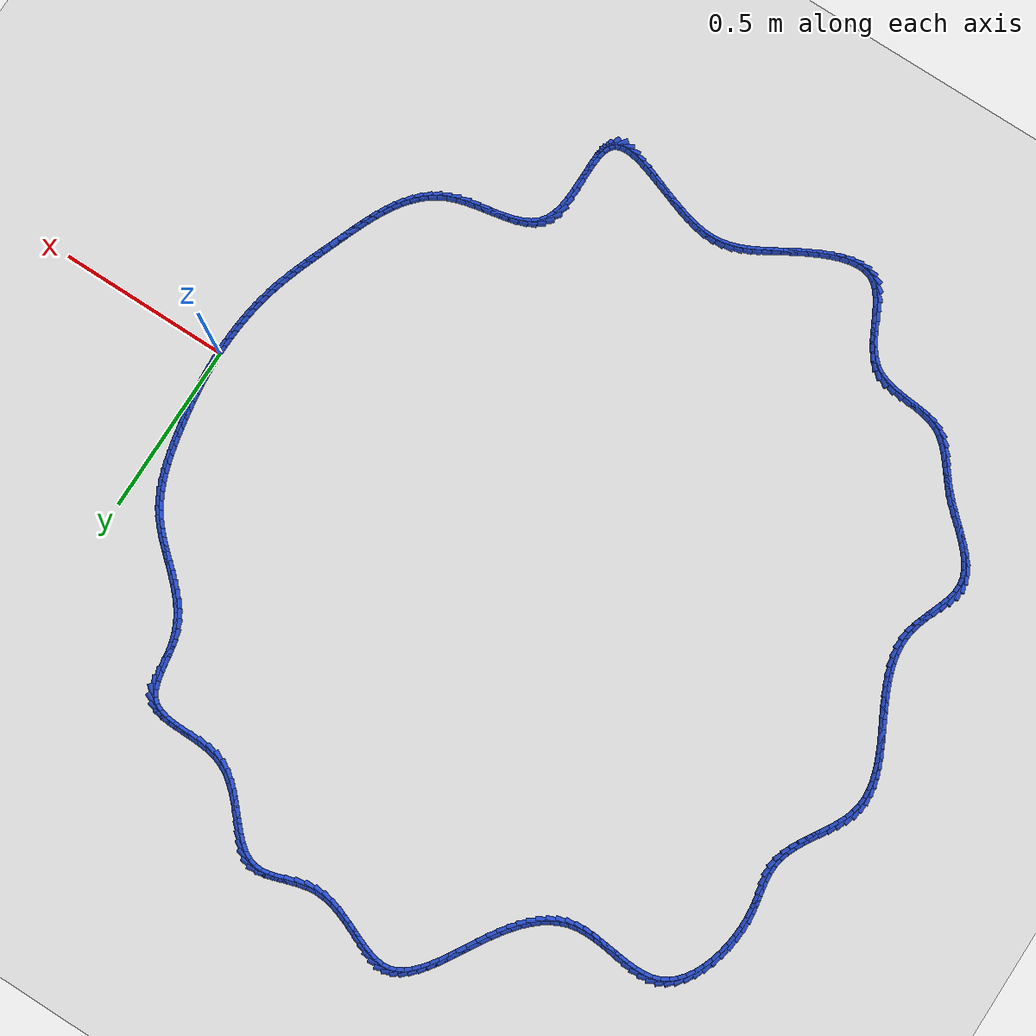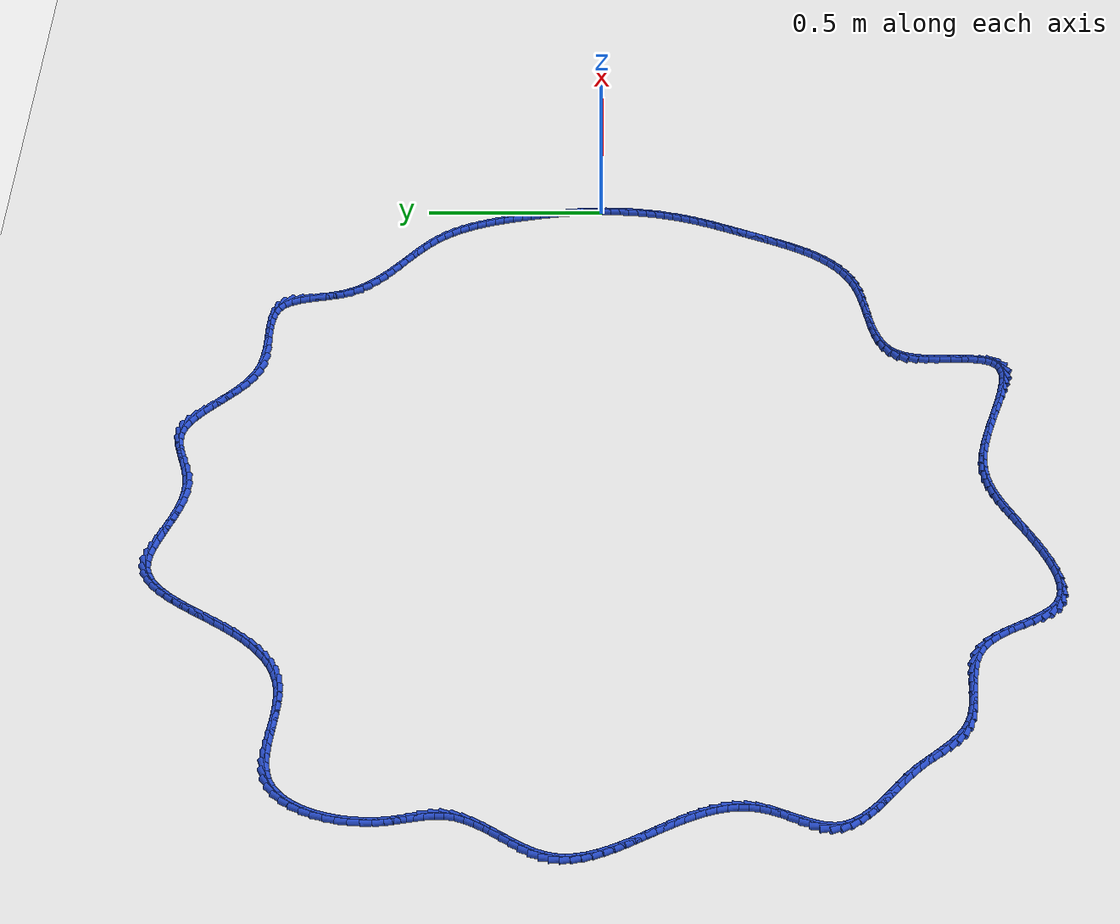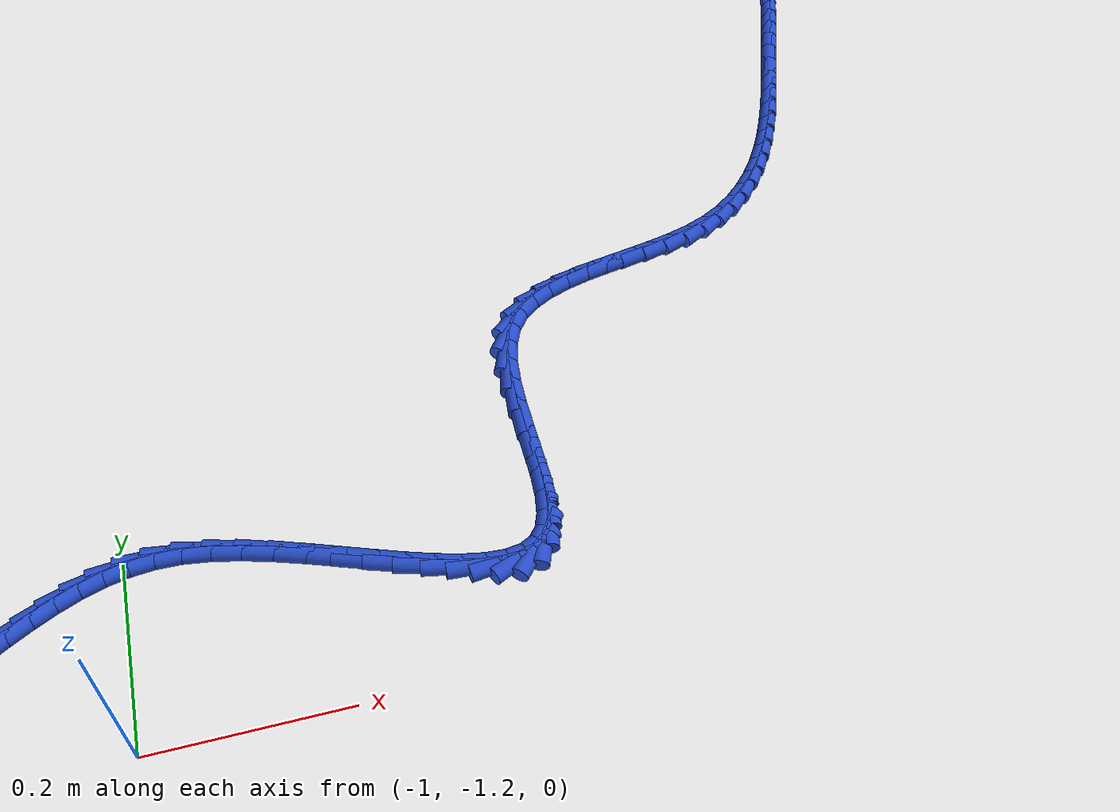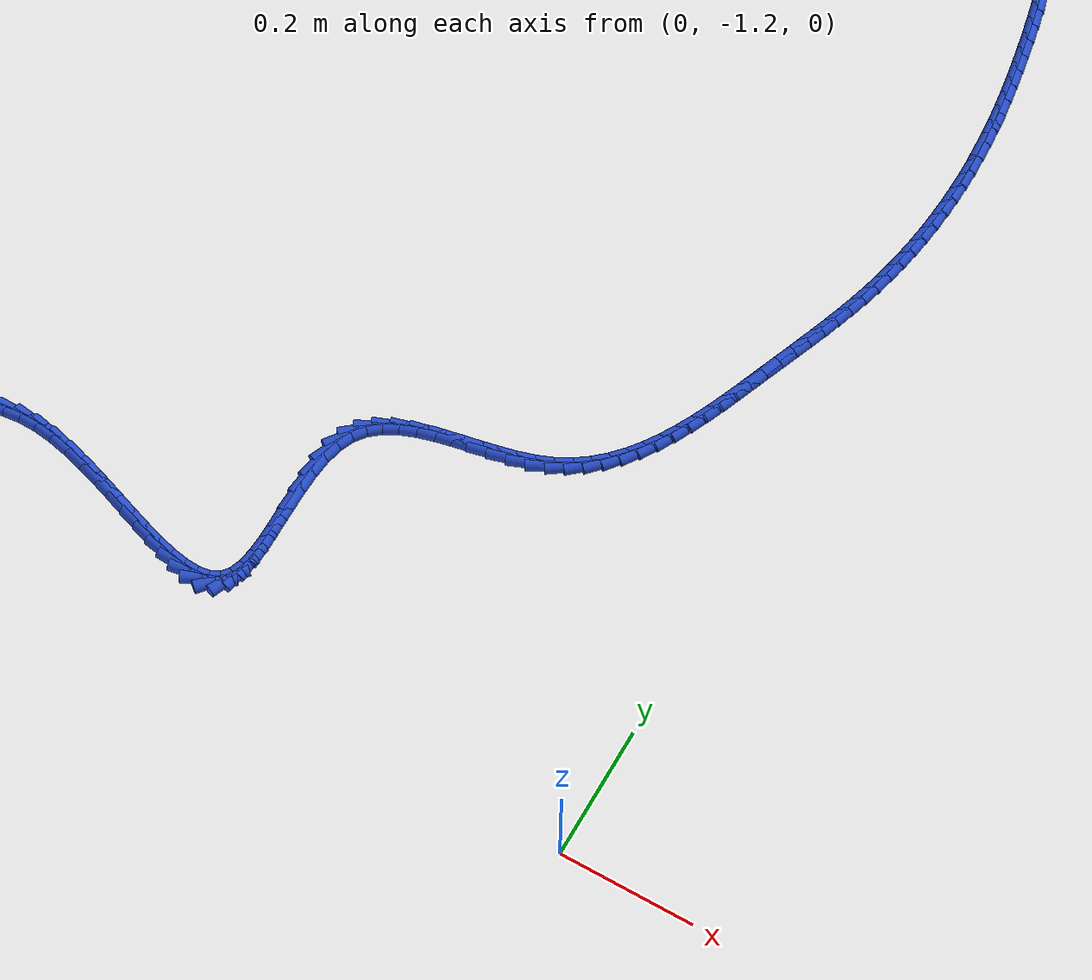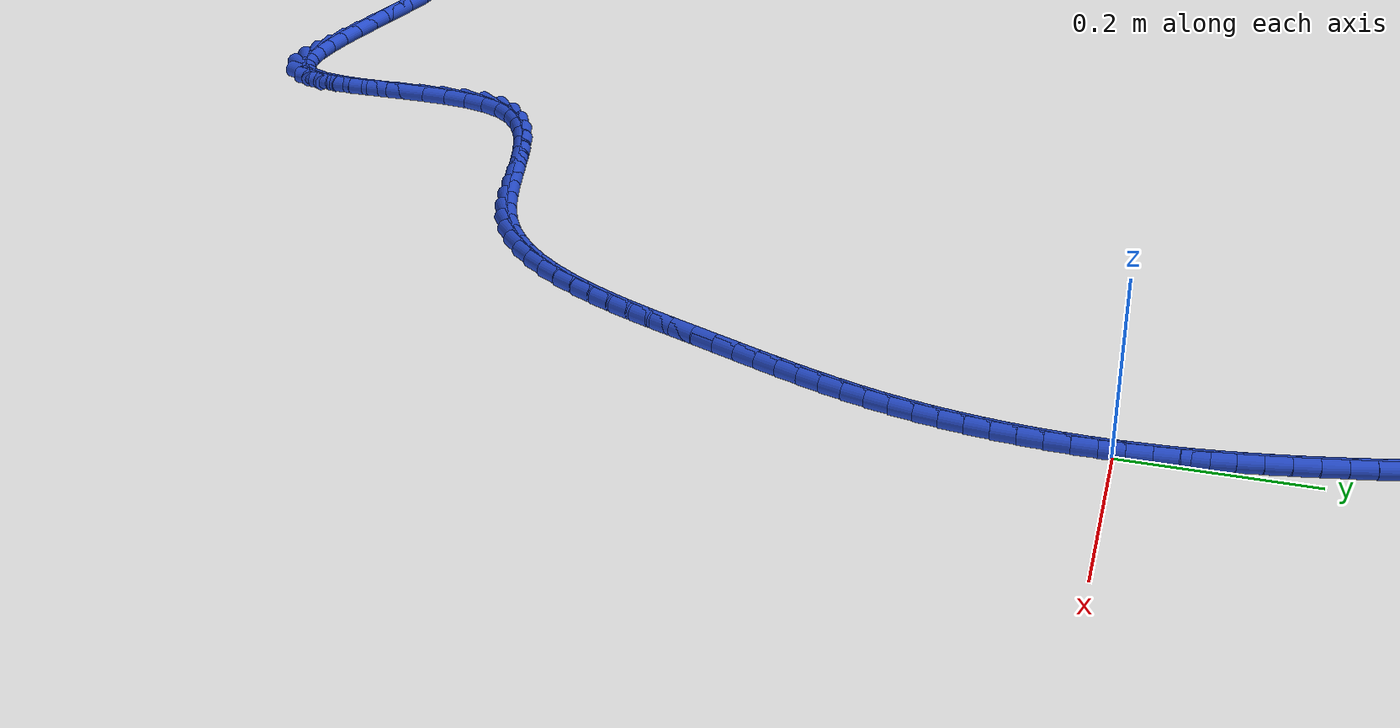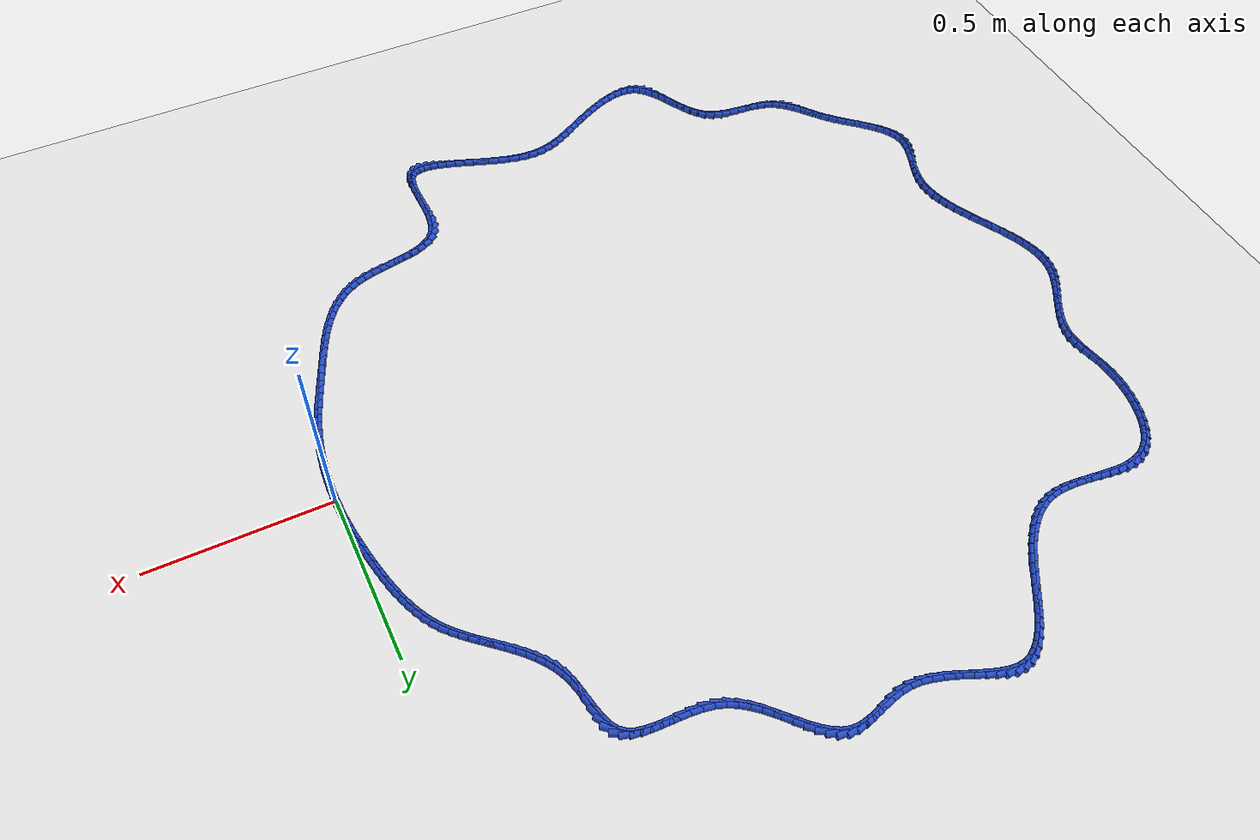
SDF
<sdf version="1.6">
 <world name="default">
  <light name="sun" type="directional">
   <pose>0 0 10 0 -0 0</pose>
   <diffuse>0.8 0.8 0.8 1</diffuse>
   <specular>0.2 0.2 0.2 1</specular>
   <attenuation>
    <range>1000</range>
    <constant>0.9</constant>
    <linear>0.01</linear>
    <quadratic>0.001</quadratic>
   </attenuation>
   <direction>-0.5 0.1 -0.9</direction>
  </light>
  <model name="ground_plane">
   <static>1</static>
   <link name="link">
    <collision name="collision">
     <geometry><plane><normal>0 0 1</normal><size>100 100</size></plane></geometry>
     <surface><friction><ode><mu>100</mu><mu2>50</mu2></ode></friction></surface>
    </collision>
    <visual name="visual">
     <cast_shadows>0</cast_shadows>
     <geometry><plane><normal>0 0 1</normal><size>100 100</size></plane></geometry>
     <material>
      <script><uri>file://media/materials/scripts/gazebo.material</uri><name>Gazebo/WhiteGlow</name></script>
     </material>
    </visual>
   </link>
  </model>
  <gravity>0 0 -9.8</gravity>
  <magnetic_field>6e-06 2.3e-05 -4.2e-05</magnetic_field>
  <atmosphere type="adiabatic"/>
  <physics name="default_physics" default="0" type="ode">
   <max_step_size>0.001</max_step_size>
   <real_time_factor>1</real_time_factor>
   <real_time_update_rate>1000</real_time_update_rate>
  </physics>
  <scene><ambient>0.4 0.4 0.4 1</ambient><background>0.7 0.7 0.7 1</background><shadows>1</shadows></scene>
  <spherical_coordinates>
   <surface_model>EARTH_WGS84</surface_model>
   <latitude_deg>0</latitude_deg>
   <longitude_deg>0</longitude_deg>
   <elevation>0</elevation>
   <heading_deg>0</heading_deg>
  </spherical_coordinates>
  <model name="line">
   <link name="link_0">
    <pose>-1.3010426069826053e-18 -6.938893903907228e-18 0.01 0 1.57 -1.5448453036828746</pose>
    <collision name="collision">
     <geometry><cylinder><radius>0.01</radius><length>0.08</length></cylinder></geometry>
    </collision>
    <visual name="visual">
     <material>
      <script><name>Gazebo/Blue</name><uri>file://media/materials/scripts/gazebo.material</uri></script>
     </material>
     <geometry><cylinder><radius>0.01</radius><length>0.08</length></cylinder></geometry>
    </visual>
   </link>
   <link name="link_1">
    <pose>-0.0006734218720668165 0.025943897823569505 0.01 0 1.57 -1.5183345414615108</pose>
    <collision name="collision">
     <geometry><cylinder><radius>0.01</radius><length>0.08</length></cylinder></geometry>
    </collision>
    <visual name="visual">
     <material>
      <script><name>Gazebo/Blue</name><uri>file://media/materials/scripts/gazebo.material</uri></script>
     </material>
     <geometry><cylinder><radius>0.01</radius><length>0.08</length></cylinder></geometry>
    </visual>
   </link>
   <link name="link_2">
    <pose>-0.002030877806275513 0.051795293260185636 0.01 0 1.57 -1.4934831011588694</pose>
    <collision name="collision">
     <geometry><cylinder><radius>0.01</radius><length>0.08</length></cylinder></geometry>
    </collision>
    <visual name="visual">
     <material>
      <script><name>Gazebo/Blue</name><uri>file://media/materials/scripts/gazebo.material</uri></script>
     </material>
     <geometry><cylinder><radius>0.01</radius><length>0.08</length></cylinder></geometry>
    </visual>
   </link>
   <link name="link_3">
    <pose>-0.004028531694577257 0.0775822407005232 0.01 0 1.57 -1.4703987092895088</pose>
    <collision name="collision">
     <geometry><cylinder><radius>0.01</radius><length>0.08</length></cylinder></geometry>
    </collision>
    <visual name="visual">
     <material>
      <script><name>Gazebo/Blue</name><uri>file://media/materials/scripts/gazebo.material</uri></script>
     </material>
     <geometry><cylinder><radius>0.01</radius><length>0.08</length></cylinder></geometry>
    </visual>
   </link>
   <link name="link_4">
    <pose>-0.006622547428923207 0.10333279453525693 0.01 0 1.57 -1.4491669388248505</pose>
    <collision name="collision">
     <geometry><cylinder><radius>0.01</radius><length>0.08</length></cylinder></geometry>
    </collision>
    <visual name="visual">
     <material>
      <script><name>Gazebo/Blue</name><uri>file://media/materials/scripts/gazebo.material</uri></script>
     </material>
     <geometry><cylinder><radius>0.01</radius><length>0.08</length></cylinder></geometry>
    </visual>
   </link>
   <link name="link_5">
    <pose>-0.00976908890126453 0.1290750091550616 0.01 0 1.57 -1.4298521132547735</pose>
    <collision name="collision">
     <geometry><cylinder><radius>0.01</radius><length>0.08</length></cylinder></geometry>
    </collision>
    <visual name="visual">
     <material>
      <script><name>Gazebo/Blue</name><uri>file://media/materials/scripts/gazebo.material</uri></script>
     </material>
     <geometry><cylinder><radius>0.01</radius><length>0.08</length></cylinder></geometry>
    </visual>
   </link>
   <link name="link_6">
    <pose>-0.013424320003552398 0.15483693895061207 0.01 0 1.57 -1.4124987397937656</pose>
    <collision name="collision">
     <geometry><cylinder><radius>0.01</radius><length>0.08</length></cylinder></geometry>
    </collision>
    <visual name="visual">
     <material>
      <script><name>Gazebo/Blue</name><uri>file://media/materials/scripts/gazebo.material</uri></script>
     </material>
     <geometry><cylinder><radius>0.01</radius><length>0.08</length></cylinder></geometry>
    </visual>
   </link>
   <link name="link_7">
    <pose>-0.01754440462773796 0.180646638312583 0.01 0 1.57 -1.397133292789064</pose>
    <collision name="collision">
     <geometry><cylinder><radius>0.01</radius><length>0.08</length></cylinder></geometry>
    </collision>
    <visual name="visual">
     <material>
      <script><name>Gazebo/Blue</name><uri>file://media/materials/scripts/gazebo.material</uri></script>
     </material>
     <geometry><cylinder><radius>0.01</radius><length>0.08</length></cylinder></geometry>
    </visual>
   </link>
   <link name="link_8">
    <pose>-0.022085506665772393 0.20653216163164934 0.01 0 1.57 -1.3836915060591704</pose>
    <collision name="collision">
     <geometry><cylinder><radius>0.01</radius><length>0.08</length></cylinder></geometry>
    </collision>
    <visual name="visual">
     <material>
      <script><name>Gazebo/Blue</name><uri>file://media/materials/scripts/gazebo.material</uri></script>
     </material>
     <geometry><cylinder><radius>0.01</radius><length>0.08</length></cylinder></geometry>
    </visual>
   </link>
   <link name="link_9">
    <pose>-0.027005510231305995 0.23252003083410824 0.01 0 1.57 -1.368972413794788</pose>
    <collision name="collision">
     <geometry><cylinder><radius>0.01</radius><length>0.08</length></cylinder></geometry>
    </collision>
    <visual name="visual">
     <material>
      <script><name>Gazebo/Blue</name><uri>file://media/materials/scripts/gazebo.material</uri></script>
     </material>
     <geometry><cylinder><radius>0.01</radius><length>0.08</length></cylinder></geometry>
    </visual>
   </link>
   <link name="link_10">
    <pose>-0.0323358404977038 0.2585712535847264 0.01 0 1.57 -1.3485805054940045</pose>
    <collision name="collision">
     <geometry><cylinder><radius>0.01</radius><length>0.08</length></cylinder></geometry>
    </collision>
    <visual name="visual">
     <material>
      <script><name>Gazebo/Blue</name><uri>file://media/materials/scripts/gazebo.material</uri></script>
     </material>
     <geometry><cylinder><radius>0.01</radius><length>0.08</length></cylinder></geometry>
    </visual>
   </link>
   <link name="link_11">
    <pose>-0.03820750189583267 0.2845581270844244 0.01 0 1.57 -1.3220276555043413</pose>
    <collision name="collision">
     <geometry><cylinder><radius>0.01</radius><length>0.08</length></cylinder></geometry>
    </collision>
    <visual name="visual">
     <material>
      <script><name>Gazebo/Blue</name><uri>file://media/materials/scripts/gazebo.material</uri></script>
     </material>
     <geometry><cylinder><radius>0.01</radius><length>0.08</length></cylinder></geometry>
    </visual>
   </link>
   <link name="link_12">
    <pose>-0.044758577165378594 0.3103466428026448 0.01 0 1.57 -1.2890358217307072</pose>
    <collision name="collision">
     <geometry><cylinder><radius>0.01</radius><length>0.08</length></cylinder></geometry>
    </collision>
    <visual name="visual">
     <material>
      <script><name>Gazebo/Blue</name><uri>file://media/materials/scripts/gazebo.material</uri></script>
     </material>
     <geometry><cylinder><radius>0.01</radius><length>0.08</length></cylinder></geometry>
    </visual>
   </link>
   <link name="link_13">
    <pose>-0.0521271490460275 0.3358027922088299 0.01 0 1.57 -1.2492537222892313</pose>
    <collision name="collision">
     <geometry><cylinder><radius>0.01</radius><length>0.08</length></cylinder></geometry>
    </collision>
    <visual name="visual">
     <material>
      <script><name>Gazebo/Blue</name><uri>file://media/materials/scripts/gazebo.material</uri></script>
     </material>
     <geometry><cylinder><radius>0.01</radius><length>0.08</length></cylinder></geometry>
    </visual>
   </link>
   <link name="link_14">
    <pose>-0.0604513002774654 0.36079256677242244 0.01 0 1.57 -1.2022916803627839</pose>
    <collision name="collision">
     <geometry><cylinder><radius>0.01</radius><length>0.08</length></cylinder></geometry>
    </collision>
    <visual name="visual">
     <material>
      <script><name>Gazebo/Blue</name><uri>file://media/materials/scripts/gazebo.material</uri></script>
     </material>
     <geometry><cylinder><radius>0.01</radius><length>0.08</length></cylinder></geometry>
    </visual>
   </link>
   <link name="link_15">
    <pose>-0.06986911359937828 0.385181957962865 0.01 0 1.57 -1.1477733697549646</pose>
    <collision name="collision">
     <geometry><cylinder><radius>0.01</radius><length>0.08</length></cylinder></geometry>
    </collision>
    <visual name="visual">
     <material>
      <script><name>Gazebo/Blue</name><uri>file://media/materials/scripts/gazebo.material</uri></script>
     </material>
     <geometry><cylinder><radius>0.01</radius><length>0.08</length></cylinder></geometry>
    </visual>
   </link>
   <link name="link_16">
    <pose>-0.08051867175145208 0.4088369572495997 0.01 0 1.57 -1.085410235722841</pose>
    <collision name="collision">
     <geometry><cylinder><radius>0.01</radius><length>0.08</length></cylinder></geometry>
    </collision>
    <visual name="visual">
     <material>
      <script><name>Gazebo/Blue</name><uri>file://media/materials/scripts/gazebo.material</uri></script>
     </material>
     <geometry><cylinder><radius>0.01</radius><length>0.08</length></cylinder></geometry>
    </visual>
   </link>
   <link name="link_17">
    <pose>-0.09253805747337282 0.4316235561020696 0.01 0 1.57 -1.0151013114527625</pose>
    <collision name="collision">
     <geometry><cylinder><radius>0.01</radius><length>0.08</length></cylinder></geometry>
    </collision>
    <visual name="visual">
     <material>
      <script><name>Gazebo/Blue</name><uri>file://media/materials/scripts/gazebo.material</uri></script>
     </material>
     <geometry><cylinder><radius>0.01</radius><length>0.08</length></cylinder></geometry>
    </visual>
   </link>
   <link name="link_18">
    <pose>-0.10606535350482643 0.45340774598971684 0.01 0 1.57 -0.9373254929409379</pose>
    <collision name="collision">
     <geometry><cylinder><radius>0.01</radius><length>0.08</length></cylinder></geometry>
    </collision>
    <visual name="visual">
     <material>
      <script><name>Gazebo/Blue</name><uri>file://media/materials/scripts/gazebo.material</uri></script>
     </material>
     <geometry><cylinder><radius>0.01</radius><length>0.08</length></cylinder></geometry>
    </visual>
   </link>
   <link name="link_19">
    <pose>-0.12123320188538461 0.47405989148138417 0.01 0 1.57 -0.8628337482914706</pose>
    <collision name="collision">
     <geometry><cylinder><radius>0.01</radius><length>0.08</length></cylinder></geometry>
    </collision>
    <visual name="visual">
     <material>
      <script><name>Gazebo/Blue</name><uri>file://media/materials/scripts/gazebo.material</uri></script>
     </material>
     <geometry><cylinder><radius>0.01</radius><length>0.08</length></cylinder></geometry>
    </visual>
   </link>
   <link name="link_20">
    <pose>-0.13797107513092582 0.49361365975468136 0.01 0 1.57 -0.8050061343336946</pose>
    <collision name="collision">
     <geometry><cylinder><radius>0.01</radius><length>0.08</length></cylinder></geometry>
    </collision>
    <visual name="visual">
     <material>
      <script><name>Gazebo/Blue</name><uri>file://media/materials/scripts/gazebo.material</uri></script>
     </material>
     <geometry><cylinder><radius>0.01</radius><length>0.08</length></cylinder></geometry>
    </visual>
   </link>
   <link name="link_21">
    <pose>-0.15594924602411453 0.5123110562844987 0.01 0 1.57 -0.7644291066043009</pose>
    <collision name="collision">
     <geometry><cylinder><radius>0.01</radius><length>0.08</length></cylinder></geometry>
    </collision>
    <visual name="visual">
     <material>
      <script><name>Gazebo/Blue</name><uri>file://media/materials/scripts/gazebo.material</uri></script>
     </material>
     <geometry><cylinder><radius>0.01</radius><length>0.08</length></cylinder></geometry>
    </visual>
   </link>
   <link name="link_22">
    <pose>-0.17482113180917527 0.530407634608199 0.01 0 1.57 -0.7405616900080769</pose>
    <collision name="collision">
     <geometry><cylinder><radius>0.01</radius><length>0.08</length></cylinder></geometry>
    </collision>
    <visual name="visual">
     <material>
      <script><name>Gazebo/Blue</name><uri>file://media/materials/scripts/gazebo.material</uri></script>
     </material>
     <geometry><cylinder><radius>0.01</radius><length>0.08</length></cylinder></geometry>
    </visual>
   </link>
   <link name="link_23">
    <pose>-0.19424014973033246 0.5481589482631446 0.01 0 1.57 -0.7329275036203929</pose>
    <collision name="collision">
     <geometry><cylinder><radius>0.01</radius><length>0.08</length></cylinder></geometry>
    </collision>
    <visual name="visual">
     <material>
      <script><name>Gazebo/Blue</name><uri>file://media/materials/scripts/gazebo.material</uri></script>
     </material>
     <geometry><cylinder><radius>0.01</radius><length>0.08</length></cylinder></geometry>
    </visual>
   </link>
   <link name="link_24">
    <pose>-0.21385971703181053 0.5658205507866981 0.01 0 1.57 -0.7412968626940298</pose>
    <collision name="collision">
     <geometry><cylinder><radius>0.01</radius><length>0.08</length></cylinder></geometry>
    </collision>
    <visual name="visual">
     <material>
      <script><name>Gazebo/Blue</name><uri>file://media/materials/scripts/gazebo.material</uri></script>
     </material>
     <geometry><cylinder><radius>0.01</radius><length>0.08</length></cylinder></geometry>
    </visual>
   </link>
   <link name="link_25">
    <pose>-0.233333250957834 0.583647995716222 0.01 0 1.57 -0.7657369403799325</pose>
    <collision name="collision">
     <geometry><cylinder><radius>0.01</radius><length>0.08</length></cylinder></geometry>
    </collision>
    <visual name="visual">
     <material>
      <script><name>Gazebo/Blue</name><uri>file://media/materials/scripts/gazebo.material</uri></script>
     </material>
     <geometry><cylinder><radius>0.01</radius><length>0.08</length></cylinder></geometry>
    </visual>
   </link>
   <link name="link_26">
    <pose>-0.25231416875262735 0.601896836589079 0.01 0 1.57 -0.8065475352843584</pose>
    <collision name="collision">
     <geometry><cylinder><radius>0.01</radius><length>0.08</length></cylinder></geometry>
    </collision>
    <visual name="visual">
     <material>
      <script><name>Gazebo/Blue</name><uri>file://media/materials/scripts/gazebo.material</uri></script>
     </material>
     <geometry><cylinder><radius>0.01</radius><length>0.08</length></cylinder></geometry>
    </visual>
   </link>
   <link name="link_27">
    <pose>-0.270455887660415 0.6208226269426316 0.01 0 1.57 -0.8640733188638222</pose>
    <collision name="collision">
     <geometry><cylinder><radius>0.01</radius><length>0.08</length></cylinder></geometry>
    </collision>
    <visual name="visual">
     <material>
      <script><name>Gazebo/Blue</name><uri>file://media/materials/scripts/gazebo.material</uri></script>
     </material>
     <geometry><cylinder><radius>0.01</radius><length>0.08</length></cylinder></geometry>
    </visual>
   </link>
   <link name="link_28">
    <pose>-0.28741182492542144 0.6406809203142421 0.01 0 1.57 -0.9383694341646547</pose>
    <collision name="collision">
     <geometry><cylinder><radius>0.01</radius><length>0.08</length></cylinder></geometry>
    </collision>
    <visual name="visual">
     <material>
      <script><name>Gazebo/Blue</name><uri>file://media/materials/scripts/gazebo.material</uri></script>
     </material>
     <geometry><cylinder><radius>0.01</radius><length>0.08</length></cylinder></geometry>
    </visual>
   </link>
   <link name="link_29">
    <pose>-0.30283539779187113 0.6617272702412733 0.01 0 1.57 -1.028722513832776</pose>
    <collision name="collision">
     <geometry><cylinder><radius>0.01</radius><length>0.08</length></cylinder></geometry>
    </collision>
    <visual name="visual">
     <material>
      <script><name>Gazebo/Blue</name><uri>file://media/materials/scripts/gazebo.material</uri></script>
     </material>
     <geometry><cylinder><radius>0.01</radius><length>0.08</length></cylinder></geometry>
    </visual>
   </link>
   <link name="link_30">
    <pose>-0.31638002350398864 0.6842172302610879 0.01 0 1.57 -1.133122792511532</pose>
    <collision name="collision">
     <geometry><cylinder><radius>0.01</radius><length>0.08</length></cylinder></geometry>
    </collision>
    <visual name="visual">
     <material>
      <script><name>Gazebo/Blue</name><uri>file://media/materials/scripts/gazebo.material</uri></script>
     </material>
     <geometry><cylinder><radius>0.01</radius><length>0.08</length></cylinder></geometry>
    </visual>
   </link>
   <link name="link_31">
    <pose>-0.3276991193059984 0.7084063539110481 0.01 0 1.57 -1.2474060621924192</pose>
    <collision name="collision">
     <geometry><cylinder><radius>0.01</radius><length>0.08</length></cylinder></geometry>
    </collision>
    <visual name="visual">
     <material>
      <script><name>Gazebo/Blue</name><uri>file://media/materials/scripts/gazebo.material</uri></script>
     </material>
     <geometry><cylinder><radius>0.01</radius><length>0.08</length></cylinder></geometry>
    </visual>
   </link>
   <link name="link_32">
    <pose>-0.3364576573358799 0.7345390562323103 0.01 0 1.57 -1.3432105040270967</pose>
    <collision name="collision">
     <geometry><cylinder><radius>0.01</radius><length>0.08</length></cylinder></geometry>
    </collision>
    <visual name="visual">
     <material>
      <script><name>Gazebo/Blue</name><uri>file://media/materials/scripts/gazebo.material</uri></script>
     </material>
     <geometry><cylinder><radius>0.01</radius><length>0.08</length></cylinder></geometry>
    </visual>
   </link>
   <link name="link_33">
    <pose>-0.34288964337292827 0.7623112245868207 0.01 0 1.57 -1.3906862748614424</pose>
    <collision name="collision">
     <geometry><cylinder><radius>0.01</radius><length>0.08</length></cylinder></geometry>
    </collision>
    <visual name="visual">
     <material>
      <script><name>Gazebo/Blue</name><uri>file://media/materials/scripts/gazebo.material</uri></script>
     </material>
     <geometry><cylinder><radius>0.01</radius><length>0.08</length></cylinder></geometry>
    </visual>
   </link>
   <link name="link_34">
    <pose>-0.3480462112570807 0.7906310646843723 0.01 0 1.57 -1.3924642275761425</pose>
    <collision name="collision">
     <geometry><cylinder><radius>0.01</radius><length>0.08</length></cylinder></geometry>
    </collision>
    <visual name="visual">
     <material>
      <script><name>Gazebo/Blue</name><uri>file://media/materials/scripts/gazebo.material</uri></script>
     </material>
     <geometry><cylinder><radius>0.01</radius><length>0.08</length></cylinder></geometry>
    </visual>
   </link>
   <link name="link_35">
    <pose>-0.3530417143281931 0.8183458409422699 0.01 0 1.57 -1.345507917384217</pose>
    <collision name="collision">
     <geometry><cylinder><radius>0.01</radius><length>0.08</length></cylinder></geometry>
    </collision>
    <visual name="visual">
     <material>
      <script><name>Gazebo/Blue</name><uri>file://media/materials/scripts/gazebo.material</uri></script>
     </material>
     <geometry><cylinder><radius>0.01</radius><length>0.08</length></cylinder></geometry>
    </visual>
   </link>
   <link name="link_36">
    <pose>-0.35899050592612103 0.8443028177778186 0.01 0 1.57 -1.236048659714106</pose>
    <collision name="collision">
     <geometry><cylinder><radius>0.01</radius><length>0.08</length></cylinder></geometry>
    </collision>
    <visual name="visual">
     <material>
      <script><name>Gazebo/Blue</name><uri>file://media/materials/scripts/gazebo.material</uri></script>
     </material>
     <geometry><cylinder><radius>0.01</radius><length>0.08</length></cylinder></geometry>
    </visual>
   </link>
   <link name="link_37">
    <pose>-0.3670069393907203 0.8673492596083233 0.01 0 1.57 -1.0378263958449676</pose>
    <collision name="collision">
     <geometry><cylinder><radius>0.01</radius><length>0.08</length></cylinder></geometry>
    </collision>
    <visual name="visual">
     <material>
      <script><name>Gazebo/Blue</name><uri>file://media/materials/scripts/gazebo.material</uri></script>
     </material>
     <geometry><cylinder><radius>0.01</radius><length>0.08</length></cylinder></geometry>
    </visual>
   </link>
   <link name="link_38">
    <pose>-0.37820536806184657 0.8863324308510889 0.01 0 1.57 -0.7340887255613944</pose>
    <collision name="collision">
     <geometry><cylinder><radius>0.01</radius><length>0.08</length></cylinder></geometry>
    </collision>
    <visual name="visual">
     <material>
      <script><name>Gazebo/Blue</name><uri>file://media/materials/scripts/gazebo.material</uri></script>
     </material>
     <geometry><cylinder><radius>0.01</radius><length>0.08</length></cylinder></geometry>
    </visual>
   </link>
   <link name="link_39">
    <pose>-0.39359885136773926 0.9002220925349297 0.01 0 1.57 -0.4350780117372672</pose>
    <collision name="collision">
     <geometry><cylinder><radius>0.01</radius><length>0.08</length></cylinder></geometry>
    </collision>
    <visual name="visual">
     <material>
      <script><name>Gazebo/Blue</name><uri>file://media/materials/scripts/gazebo.material</uri></script>
     </material>
     <geometry><cylinder><radius>0.01</radius><length>0.08</length></cylinder></geometry>
    </visual>
   </link>
   <link name="link_40">
    <pose>-0.4131196720460522 0.9092950090443633 0.01 0 1.57 -0.22816482422314488</pose>
    <collision name="collision">
     <geometry><cylinder><radius>0.01</radius><length>0.08</length></cylinder></geometry>
    </collision>
    <visual name="visual">
     <material>
      <script><name>Gazebo/Blue</name><uri>file://media/materials/scripts/gazebo.material</uri></script>
     </material>
     <geometry><cylinder><radius>0.01</radius><length>0.08</length></cylinder></geometry>
    </visual>
   </link>
   <link name="link_41">
    <pose>-0.436046194566393 0.9146187402891426 0.01 0 1.57 -0.10326282881329502</pose>
    <collision name="collision">
     <geometry><cylinder><radius>0.01</radius><length>0.08</length></cylinder></geometry>
    </collision>
    <visual name="visual">
     <material>
      <script><name>Gazebo/Blue</name><uri>file://media/materials/scripts/gazebo.material</uri></script>
     </material>
     <geometry><cylinder><radius>0.01</radius><length>0.08</length></cylinder></geometry>
    </visual>
   </link>
   <link name="link_42">
    <pose>-0.4616476769722693 0.9172718587494932 0.01 0 1.57 -0.03850160956379193</pose>
    <collision name="collision">
     <geometry><cylinder><radius>0.01</radius><length>0.08</length></cylinder></geometry>
    </collision>
    <visual name="visual">
     <material>
      <script><name>Gazebo/Blue</name><uri>file://media/materials/scripts/gazebo.material</uri></script>
     </material>
     <geometry><cylinder><radius>0.01</radius><length>0.08</length></cylinder></geometry>
    </visual>
   </link>
   <link name="link_43">
    <pose>-0.4891933773071892 0.9183329369056399 0.01 0 1.57 -0.019038937644648587</pose>
    <collision name="collision">
     <geometry><cylinder><radius>0.01</radius><length>0.08</length></cylinder></geometry>
    </collision>
    <visual name="visual">
     <material>
      <script><name>Gazebo/Blue</name><uri>file://media/materials/scripts/gazebo.material</uri></script>
     </material>
     <geometry><cylinder><radius>0.01</radius><length>0.08</length></cylinder></geometry>
    </visual>
   </link>
   <link name="link_44">
    <pose>-0.517952553614661 0.9188805472378087 0.01 0 1.57 -0.03803371212145451</pose>
    <collision name="collision">
     <geometry><cylinder><radius>0.01</radius><length>0.08</length></cylinder></geometry>
    </collision>
    <visual name="visual">
     <material>
      <script><name>Gazebo/Blue</name><uri>file://media/materials/scripts/gazebo.material</uri></script>
     </material>
     <geometry><cylinder><radius>0.01</radius><length>0.08</length></cylinder></geometry>
    </visual>
   </link>
   <link name="link_45">
    <pose>-0.5471944639381919 0.9199932622262242 0.01 0 1.57 -0.09478313095866771</pose>
    <collision name="collision">
     <geometry><cylinder><radius>0.01</radius><length>0.08</length></cylinder></geometry>
    </collision>
    <visual name="visual">
     <material>
      <script><name>Gazebo/Blue</name><uri>file://media/materials/scripts/gazebo.material</uri></script>
     </material>
     <geometry><cylinder><radius>0.01</radius><length>0.08</length></cylinder></geometry>
    </visual>
   </link>
   <link name="link_46">
    <pose>-0.5761883663212908 0.9227496543511126 0.01 0 1.57 -0.19312265586813135</pose>
    <collision name="collision">
     <geometry><cylinder><radius>0.01</radius><length>0.08</length></cylinder></geometry>
    </collision>
    <visual name="visual">
     <material>
      <script><name>Gazebo/Blue</name><uri>file://media/materials/scripts/gazebo.material</uri></script>
     </material>
     <geometry><cylinder><radius>0.01</radius><length>0.08</length></cylinder></geometry>
    </visual>
   </link>
   <link name="link_47">
    <pose>-0.6042035188074648 0.9282282960926986 0.01 0 1.57 -0.3383980068140878</pose>
    <collision name="collision">
     <geometry><cylinder><radius>0.01</radius><length>0.08</length></cylinder></geometry>
    </collision>
    <visual name="visual">
     <material>
      <script><name>Gazebo/Blue</name><uri>file://media/materials/scripts/gazebo.material</uri></script>
     </material>
     <geometry><cylinder><radius>0.01</radius><length>0.08</length></cylinder></geometry>
    </visual>
   </link>
   <link name="link_48">
    <pose>-0.6305188542791111 0.9374895954475316 0.01 0 1.57 -0.5010439191679373</pose>
    <collision name="collision">
     <geometry><cylinder><radius>0.01</radius><length>0.08</length></cylinder></geometry>
    </collision>
    <visual name="visual">
     <material>
      <script><name>Gazebo/Blue</name><uri>file://media/materials/scripts/gazebo.material</uri></script>
     </material>
     <geometry><cylinder><radius>0.01</radius><length>0.08</length></cylinder></geometry>
    </visual>
   </link>
   <link name="link_49">
    <pose>-0.6548332208401827 0.9508055707267604 0.01 0 1.57 -0.6329286771304352</pose>
    <collision name="collision">
     <geometry><cylinder><radius>0.01</radius><length>0.08</length></cylinder></geometry>
    </collision>
    <visual name="visual">
     <material>
      <script><name>Gazebo/Blue</name><uri>file://media/materials/scripts/gazebo.material</uri></script>
     </material>
     <geometry><cylinder><radius>0.01</radius><length>0.08</length></cylinder></geometry>
    </visual>
   </link>
   <link name="link_50">
    <pose>-0.6774177401152314 0.96737379826443 0.01 0 1.57 -0.7299570894741478</pose>
    <collision name="collision">
     <geometry><cylinder><radius>0.01</radius><length>0.08</length></cylinder></geometry>
    </collision>
    <visual name="visual">
     <material>
      <script><name>Gazebo/Blue</name><uri>file://media/materials/scripts/gazebo.material</uri></script>
     </material>
     <geometry><cylinder><radius>0.01</radius><length>0.08</length></cylinder></geometry>
    </visual>
   </link>
   <link name="link_51">
    <pose>-0.6985845985600144 0.9863147552857819 0.01 0 1.57 -0.7946033513987176</pose>
    <collision name="collision">
     <geometry><cylinder><radius>0.01</radius><length>0.08</length></cylinder></geometry>
    </collision>
    <visual name="visual">
     <material>
      <script><name>Gazebo/Blue</name><uri>file://media/materials/scripts/gazebo.material</uri></script>
     </material>
     <geometry><cylinder><radius>0.01</radius><length>0.08</length></cylinder></geometry>
    </visual>
   </link>
   <link name="link_52">
    <pose>-0.7186459826302888 1.0067489190160561 0.01 0 1.57 -0.8295146238784223</pose>
    <collision name="collision">
     <geometry><cylinder><radius>0.01</radius><length>0.08</length></cylinder></geometry>
    </collision>
    <visual name="visual">
     <material>
      <script><name>Gazebo/Blue</name><uri>file://media/materials/scripts/gazebo.material</uri></script>
     </material>
     <geometry><cylinder><radius>0.01</radius><length>0.08</length></cylinder></geometry>
    </visual>
   </link>
   <link name="link_53">
    <pose>-0.7379140787818119 1.0277967666804937 0.01 0 1.57 -0.8357741159360251</pose>
    <collision name="collision">
     <geometry><cylinder><radius>0.01</radius><length>0.08</length></cylinder></geometry>
    </collision>
    <visual name="visual">
     <material>
      <script><name>Gazebo/Blue</name><uri>file://media/materials/scripts/gazebo.material</uri></script>
     </material>
     <geometry><cylinder><radius>0.01</radius><length>0.08</length></cylinder></geometry>
    </visual>
   </link>
   <link name="link_54">
    <pose>-0.7567010734703409 1.0485787755043354 0.01 0 1.57 -0.8120178000085374</pose>
    <collision name="collision">
     <geometry><cylinder><radius>0.01</radius><length>0.08</length></cylinder></geometry>
    </collision>
    <visual name="visual">
     <material>
      <script><name>Gazebo/Blue</name><uri>file://media/materials/scripts/gazebo.material</uri></script>
     </material>
     <geometry><cylinder><radius>0.01</radius><length>0.08</length></cylinder></geometry>
    </visual>
   </link>
   <link name="link_55">
    <pose>-0.7753191531516332 1.068215422712822 0.01 0 1.57 -0.7538032395687636</pose>
    <collision name="collision">
     <geometry><cylinder><radius>0.01</radius><length>0.08</length></cylinder></geometry>
    </collision>
    <visual name="visual">
     <material>
      <script><name>Gazebo/Blue</name><uri>file://media/materials/scripts/gazebo.material</uri></script>
     </material>
     <geometry><cylinder><radius>0.01</radius><length>0.08</length></cylinder></geometry>
    </visual>
   </link>
   <link name="link_56">
    <pose>-0.7940805042814458 1.085827185531194 0.01 0 1.57 -0.653245426393471</pose>
    <collision name="collision">
     <geometry><cylinder><radius>0.01</radius><length>0.08</length></cylinder></geometry>
    </collision>
    <visual name="visual">
     <material>
      <script><name>Gazebo/Blue</name><uri>file://media/materials/scripts/gazebo.material</uri></script>
     </material>
     <geometry><cylinder><radius>0.01</radius><length>0.08</length></cylinder></geometry>
    </visual>
   </link>
   <link name="link_57">
    <pose>-0.813297313315536 1.1005345411846925 0.01 0 1.57 -0.5002261512844658</pose>
    <collision name="collision">
     <geometry><cylinder><radius>0.01</radius><length>0.08</length></cylinder></geometry>
    </collision>
    <visual name="visual">
     <material>
      <script><name>Gazebo/Blue</name><uri>file://media/materials/scripts/gazebo.material</uri></script>
     </material>
     <geometry><cylinder><radius>0.01</radius><length>0.08</length></cylinder></geometry>
    </visual>
   </link>
   <link name="link_58">
    <pose>-0.833281766709661 1.1114579668985582 0.01 0 1.57 -0.2888715178001583</pose>
    <collision name="collision">
     <geometry><cylinder><radius>0.01</radius><length>0.08</length></cylinder></geometry>
    </collision>
    <visual name="visual">
     <material>
      <script><name>Gazebo/Blue</name><uri>file://media/materials/scripts/gazebo.material</uri></script>
     </material>
     <geometry><cylinder><radius>0.01</radius><length>0.08</length></cylinder></geometry>
    </visual>
   </link>
   <link name="link_59">
    <pose>-0.8543460509195784 1.1177179398980324 0.01 0 1.57 -0.03962480373865633</pose>
    <collision name="collision">
     <geometry><cylinder><radius>0.01</radius><length>0.08</length></cylinder></geometry>
    </collision>
    <visual name="visual">
     <material>
      <script><name>Gazebo/Blue</name><uri>file://media/materials/scripts/gazebo.material</uri></script>
     </material>
     <geometry><cylinder><radius>0.01</radius><length>0.08</length></cylinder></geometry>
    </visual>
   </link>
   <link name="link_60">
    <pose>-0.8767658021198552 1.1186067833863966 0.01 0 1.57 0.1543996903617715</pose>
    <collision name="collision">
     <geometry><cylinder><radius>0.01</radius><length>0.08</length></cylinder></geometry>
    </collision>
    <visual name="visual">
     <material>
      <script><name>Gazebo/Blue</name><uri>file://media/materials/scripts/gazebo.material</uri></script>
     </material>
     <geometry><cylinder><radius>0.01</radius><length>0.08</length></cylinder></geometry>
    </visual>
   </link>
   <link name="link_61">
    <pose>-0.9004984145974323 1.114913076865174 0.01 0 1.57 0.26410611192535016</pose>
    <collision name="collision">
     <geometry><cylinder><radius>0.01</radius><length>0.08</length></cylinder></geometry>
    </collision>
    <visual name="visual">
     <material>
      <script><name>Gazebo/Blue</name><uri>file://media/materials/scripts/gazebo.material</uri></script>
     </material>
     <geometry><cylinder><radius>0.01</radius><length>0.08</length></cylinder></geometry>
    </visual>
   </link>
   <link name="link_62">
    <pose>-0.9253373714373765 1.1081960500164336 0.01 0 1.57 0.3075432165854948</pose>
    <collision name="collision">
     <geometry><cylinder><radius>0.01</radius><length>0.08</length></cylinder></geometry>
    </collision>
    <visual name="visual">
     <material>
      <script><name>Gazebo/Blue</name><uri>file://media/materials/scripts/gazebo.material</uri></script>
     </material>
     <geometry><cylinder><radius>0.01</radius><length>0.08</length></cylinder></geometry>
    </visual>
   </link>
   <link name="link_63">
    <pose>-0.9510747995793934 1.1000213086189083 0.01 0 1.57 0.2962557683704399</pose>
    <collision name="collision">
     <geometry><cylinder><radius>0.01</radius><length>0.08</length></cylinder></geometry>
    </collision>
    <visual name="visual">
     <material>
      <script><name>Gazebo/Blue</name><uri>file://media/materials/scripts/gazebo.material</uri></script>
     </material>
     <geometry><cylinder><radius>0.01</radius><length>0.08</length></cylinder></geometry>
    </visual>
   </link>
   <link name="link_64">
    <pose>-0.9775028259631882 1.0919544584513334 0.01 0 1.57 0.2332518977893358</pose>
    <collision name="collision">
     <geometry><cylinder><radius>0.01</radius><length>0.08</length></cylinder></geometry>
    </collision>
    <visual name="visual">
     <material>
      <script><name>Gazebo/Blue</name><uri>file://media/materials/scripts/gazebo.material</uri></script>
     </material>
     <geometry><cylinder><radius>0.01</radius><length>0.08</length></cylinder></geometry>
    </visual>
   </link>
   <link name="link_65">
    <pose>-1.004413577528466 1.0855611052924432 0.01 0 1.57 0.11552185965410673</pose>
    <collision name="collision">
     <geometry><cylinder><radius>0.01</radius><length>0.08</length></cylinder></geometry>
    </collision>
    <visual name="visual">
     <material>
      <script><name>Gazebo/Blue</name><uri>file://media/materials/scripts/gazebo.material</uri></script>
     </material>
     <geometry><cylinder><radius>0.01</radius><length>0.08</length></cylinder></geometry>
    </visual>
   </link>
   <link name="link_66">
    <pose>-1.0315991913979132 1.0824065271911665 0.01 0 1.57 -0.04093118501083047</pose>
    <collision name="collision">
     <geometry><cylinder><radius>0.01</radius><length>0.08</length></cylinder></geometry>
    </collision>
    <visual name="visual">
     <material>
      <script><name>Gazebo/Blue</name><uri>file://media/materials/scripts/gazebo.material</uri></script>
     </material>
     <geometry><cylinder><radius>0.01</radius><length>0.08</length></cylinder></geometry>
    </visual>
   </link>
   <link name="link_67">
    <pose>-1.0588683561117072 1.0835233101587076 0.01 0 1.57 -0.1747596472735226</pose>
    <collision name="collision">
     <geometry><cylinder><radius>0.01</radius><length>0.08</length></cylinder></geometry>
    </collision>
    <visual name="visual">
     <material>
      <script><name>Gazebo/Blue</name><uri>file://media/materials/scripts/gazebo.material</uri></script>
     </material>
     <geometry><cylinder><radius>0.01</radius><length>0.08</length></cylinder></geometry>
    </visual>
   </link>
   <link name="link_68">
    <pose>-1.0860799783809567 1.08832781489991 0.01 0 1.57 -0.274275102753878</pose>
    <collision name="collision">
     <geometry><cylinder><radius>0.01</radius><length>0.08</length></cylinder></geometry>
    </collision>
    <visual name="visual">
     <material>
      <script><name>Gazebo/Blue</name><uri>file://media/materials/scripts/gazebo.material</uri></script>
     </material>
     <geometry><cylinder><radius>0.01</radius><length>0.08</length></cylinder></geometry>
    </visual>
   </link>
   <link name="link_69">
    <pose>-1.1131024533649603 1.0959310252053325 0.01 0 1.57 -0.34224551649813695</pose>
    <collision name="collision">
     <geometry><cylinder><radius>0.01</radius><length>0.08</length></cylinder></geometry>
    </collision>
    <visual name="visual">
     <material>
      <script><name>Gazebo/Blue</name><uri>file://media/materials/scripts/gazebo.material</uri></script>
     </material>
     <geometry><cylinder><radius>0.01</radius><length>0.08</length></cylinder></geometry>
    </visual>
   </link>
   <link name="link_70">
    <pose>-1.139804176223016 1.1054439248655348 0.01 0 1.57 -0.38161679508487856</pose>
    <collision name="collision">
     <geometry><cylinder><radius>0.01</radius><length>0.08</length></cylinder></geometry>
    </collision>
    <visual name="visual">
     <material>
      <script><name>Gazebo/Blue</name><uri>file://media/materials/scripts/gazebo.material</uri></script>
     </material>
     <geometry><cylinder><radius>0.01</radius><length>0.08</length></cylinder></geometry>
    </visual>
   </link>
   <link name="link_71">
    <pose>-1.1660535421144216 1.1159774976710761 0.01 0 1.57 -0.39383830226272526</pose>
    <collision name="collision">
     <geometry><cylinder><radius>0.01</radius><length>0.08</length></cylinder></geometry>
    </collision>
    <visual name="visual">
     <material>
      <script><name>Gazebo/Blue</name><uri>file://media/materials/scripts/gazebo.material</uri></script>
     </material>
     <geometry><cylinder><radius>0.01</radius><length>0.08</length></cylinder></geometry>
    </visual>
   </link>
   <link name="link_72">
    <pose>-1.1917189461984745 1.126642727412515 0.01 0 1.57 -0.3780139206703971</pose>
    <collision name="collision">
     <geometry><cylinder><radius>0.01</radius><length>0.08</length></cylinder></geometry>
    </collision>
    <visual name="visual">
     <material>
      <script><name>Gazebo/Blue</name><uri>file://media/materials/scripts/gazebo.material</uri></script>
     </material>
     <geometry><cylinder><radius>0.01</radius><length>0.08</length></cylinder></geometry>
    </visual>
   </link>
   <link name="link_73">
    <pose>-1.216668783634475 1.1365505978804125 0.01 0 1.57 -0.3302128483541288</pose>
    <collision name="collision">
     <geometry><cylinder><radius>0.01</radius><length>0.08</length></cylinder></geometry>
    </collision>
    <visual name="visual">
     <material>
      <script><name>Gazebo/Blue</name><uri>file://media/materials/scripts/gazebo.material</uri></script>
     </material>
     <geometry><cylinder><radius>0.01</radius><length>0.08</length></cylinder></geometry>
    </visual>
   </link>
   <link name="link_74">
    <pose>-1.2407714495817184 1.144812092865326 0.01 0 1.57 -0.242744165373473</pose>
    <collision name="collision">
     <geometry><cylinder><radius>0.01</radius><length>0.08</length></cylinder></geometry>
    </collision>
    <visual name="visual">
     <material>
      <script><name>Gazebo/Blue</name><uri>file://media/materials/scripts/gazebo.material</uri></script>
     </material>
     <geometry><cylinder><radius>0.01</radius><length>0.08</length></cylinder></geometry>
    </visual>
   </link>
   <link name="link_75">
    <pose>-1.2638953391995043 1.150538196157816 0.01 0 1.57 -0.1041797708972424</pose>
    <collision name="collision">
     <geometry><cylinder><radius>0.01</radius><length>0.08</length></cylinder></geometry>
    </collision>
    <visual name="visual">
     <material>
      <script><name>Gazebo/Blue</name><uri>file://media/materials/scripts/gazebo.material</uri></script>
     </material>
     <geometry><cylinder><radius>0.01</radius><length>0.08</length></cylinder></geometry>
    </visual>
   </link>
   <link name="link_76">
    <pose>-1.2859088476471296 1.152839891548441 0.01 0 1.57 0.09610725460917056</pose>
    <collision name="collision">
     <geometry><cylinder><radius>0.01</radius><length>0.08</length></cylinder></geometry>
    </collision>
    <visual name="visual">
     <material>
      <script><name>Gazebo/Blue</name><uri>file://media/materials/scripts/gazebo.material</uri></script>
     </material>
     <geometry><cylinder><radius>0.01</radius><length>0.08</length></cylinder></geometry>
    </visual>
   </link>
   <link name="link_77">
    <pose>-1.306682312413387 1.1508372411845162 0.01 0 1.57 0.32896347673873627</pose>
    <collision name="collision">
     <geometry><cylinder><radius>0.01</radius><length>0.08</length></cylinder></geometry>
    </collision>
    <visual name="visual">
     <material>
      <script><name>Gazebo/Blue</name><uri>file://media/materials/scripts/gazebo.material</uri></script>
     </material>
     <geometry><cylinder><radius>0.01</radius><length>0.08</length></cylinder></geometry>
    </visual>
   </link>
   <link name="link_78">
    <pose>-1.3261983526077918 1.1441751062309726 0.01 0 1.57 0.5334759758551566</pose>
    <collision name="collision">
     <geometry><cylinder><radius>0.01</radius><length>0.08</length></cylinder></geometry>
    </collision>
    <visual name="visual">
     <material>
      <script><name>Gazebo/Blue</name><uri>file://media/materials/scripts/gazebo.material</uri></script>
     </material>
     <geometry><cylinder><radius>0.01</radius><length>0.08</length></cylinder></geometry>
    </visual>
   </link>
   <link name="link_79">
    <pose>-1.3446112185961154 1.1333005442771846 0.01 0 1.57 0.6949700475039674</pose>
    <collision name="collision">
     <geometry><cylinder><radius>0.01</radius><length>0.08</length></cylinder></geometry>
    </collision>
    <visual name="visual">
     <material>
      <script><name>Gazebo/Blue</name><uri>file://media/materials/scripts/gazebo.material</uri></script>
     </material>
     <geometry><cylinder><radius>0.01</radius><length>0.08</length></cylinder></geometry>
    </visual>
   </link>
   <link name="link_80">
    <pose>-1.3620896471388695 1.1187283216406259 0.01 0 1.57 0.8156313135336554</pose>
    <collision name="collision">
     <geometry><cylinder><radius>0.01</radius><length>0.08</length></cylinder></geometry>
    </collision>
    <visual name="visual">
     <material>
      <script><name>Gazebo/Blue</name><uri>file://media/materials/scripts/gazebo.material</uri></script>
     </material>
     <geometry><cylinder><radius>0.01</radius><length>0.08</length></cylinder></geometry>
    </visual>
   </link>
   <link name="link_81">
    <pose>-1.3788023749965659 1.10097320463877 0.01 0 1.57 0.9027437548934093</pose>
    <collision name="collision">
     <geometry><cylinder><radius>0.01</radius><length>0.08</length></cylinder></geometry>
    </collision>
    <visual name="visual">
     <material>
      <script><name>Gazebo/Blue</name><uri>file://media/materials/scripts/gazebo.material</uri></script>
     </material>
     <geometry><cylinder><radius>0.01</radius><length>0.08</length></cylinder></geometry>
    </visual>
   </link>
   <link name="link_82">
    <pose>-1.3949181389297163 1.080549959589091 0.01 0 1.57 0.9635296841840085</pose>
    <collision name="collision">
     <geometry><cylinder><radius>0.01</radius><length>0.08</length></cylinder></geometry>
    </collision>
    <visual name="visual">
     <material>
      <script><name>Gazebo/Blue</name><uri>file://media/materials/scripts/gazebo.material</uri></script>
     </material>
     <geometry><cylinder><radius>0.01</radius><length>0.08</length></cylinder></geometry>
    </visual>
   </link>
   <link name="link_83">
    <pose>-1.4106056756988328 1.0579733528090647 0.01 0 1.57 1.0035272739901535</pose>
    <collision name="collision">
     <geometry><cylinder><radius>0.01</radius><length>0.08</length></cylinder></geometry>
    </collision>
    <visual name="visual">
     <material>
      <script><name>Gazebo/Blue</name><uri>file://media/materials/scripts/gazebo.material</uri></script>
     </material>
     <geometry><cylinder><radius>0.01</radius><length>0.08</length></cylinder></geometry>
    </visual>
   </link>
   <link name="link_84">
    <pose>-1.4260337220644261 1.0337581506161635 0.01 0 1.57 1.0265010932751242</pose>
    <collision name="collision">
     <geometry><cylinder><radius>0.01</radius><length>0.08</length></cylinder></geometry>
    </collision>
    <visual name="visual">
     <material>
      <script><name>Gazebo/Blue</name><uri>file://media/materials/scripts/gazebo.material</uri></script>
     </material>
     <geometry><cylinder><radius>0.01</radius><length>0.08</length></cylinder></geometry>
    </visual>
   </link>
   <link name="link_85">
    <pose>-1.4413710147870087 1.0084191193278627 0.01 0 1.57 1.0347402237558159</pose>
    <collision name="collision">
     <geometry><cylinder><radius>0.01</radius><length>0.08</length></cylinder></geometry>
    </collision>
    <visual name="visual">
     <material>
      <script><name>Gazebo/Blue</name><uri>file://media/materials/scripts/gazebo.material</uri></script>
     </material>
     <geometry><cylinder><radius>0.01</radius><length>0.08</length></cylinder></geometry>
    </visual>
   </link>
   <link name="link_86">
    <pose>-1.4567862906270925 0.9824710252616355 0.01 0 1.57 1.0293451726246854</pose>
    <collision name="collision">
     <geometry><cylinder><radius>0.01</radius><length>0.08</length></cylinder></geometry>
    </collision>
    <visual name="visual">
     <material>
      <script><name>Gazebo/Blue</name><uri>file://media/materials/scripts/gazebo.material</uri></script>
     </material>
     <geometry><cylinder><radius>0.01</radius><length>0.08</length></cylinder></geometry>
    </visual>
   </link>
   <link name="link_87">
    <pose>-1.4724482863451887 0.9564286347349561 0.01 0 1.57 1.0104097593267476</pose>
    <collision name="collision">
     <geometry><cylinder><radius>0.01</radius><length>0.08</length></cylinder></geometry>
    </collision>
    <visual name="visual">
     <material>
      <script><name>Gazebo/Blue</name><uri>file://media/materials/scripts/gazebo.material</uri></script>
     </material>
     <geometry><cylinder><radius>0.01</radius><length>0.08</length></cylinder></geometry>
    </visual>
   </link>
   <link name="link_88">
    <pose>-1.4885257387018087 0.9308067140652994 0.01 0 1.57 0.9770985973906198</pose>
    <collision name="collision">
     <geometry><cylinder><radius>0.01</radius><length>0.08</length></cylinder></geometry>
    </collision>
    <visual name="visual">
     <material>
      <script><name>Gazebo/Blue</name><uri>file://media/materials/scripts/gazebo.material</uri></script>
     </material>
     <geometry><cylinder><radius>0.01</radius><length>0.08</length></cylinder></geometry>
    </visual>
   </link>
   <link name="link_89">
    <pose>-1.5051873844574648 0.9061200295701389 0.01 0 1.57 0.9285931761300371</pose>
    <collision name="collision">
     <geometry><cylinder><radius>0.01</radius><length>0.08</length></cylinder></geometry>
    </collision>
    <visual name="visual">
     <material>
      <script><name>Gazebo/Blue</name><uri>file://media/materials/scripts/gazebo.material</uri></script>
     </material>
     <geometry><cylinder><radius>0.01</radius><length>0.08</length></cylinder></geometry>
    </visual>
   </link>
   <link name="link_90">
    <pose>-1.5225901493694949 0.8828534895990602 0.01 0 1.57 0.8675562680609067</pose>
    <collision name="collision">
     <geometry><cylinder><radius>0.01</radius><length>0.08</length></cylinder></geometry>
    </collision>
    <visual name="visual">
     <material>
      <script><name>Gazebo/Blue</name><uri>file://media/materials/scripts/gazebo.material</uri></script>
     </material>
     <geometry><cylinder><radius>0.01</radius><length>0.08</length></cylinder></geometry>
    </visual>
   </link>
   <link name="link_91">
    <pose>-1.540830628852636 0.8613394886630191 0.01 0 1.57 0.793734327743835</pose>
    <collision name="collision">
     <geometry><cylinder><radius>0.01</radius><length>0.08</length></cylinder></geometry>
    </collision>
    <visual name="visual">
     <material>
      <script><name>Gazebo/Blue</name><uri>file://media/materials/scripts/gazebo.material</uri></script>
     </material>
     <geometry><cylinder><radius>0.01</radius><length>0.08</length></cylinder></geometry>
    </visual>
   </link>
   <link name="link_92">
    <pose>-1.5599862055209726 0.8418618517165609 0.01 0 1.57 0.7054046833538778</pose>
    <collision name="collision">
     <geometry><cylinder><radius>0.01</radius><length>0.08</length></cylinder></geometry>
    </collision>
    <visual name="visual">
     <material>
      <script><name>Gazebo/Blue</name><uri>file://media/materials/scripts/gazebo.material</uri></script>
     </material>
     <geometry><cylinder><radius>0.01</radius><length>0.08</length></cylinder></geometry>
    </visual>
   </link>
   <link name="link_93">
    <pose>-1.5801342538379344 0.8247043831095431 0.01 0 1.57 0.6012046176604026</pose>
    <collision name="collision">
     <geometry><cylinder><radius>0.01</radius><length>0.08</length></cylinder></geometry>
    </collision>
    <visual name="visual">
     <material>
      <script><name>Gazebo/Blue</name><uri>file://media/materials/scripts/gazebo.material</uri></script>
     </material>
     <geometry><cylinder><radius>0.01</radius><length>0.08</length></cylinder></geometry>
    </visual>
   </link>
   <link name="link_94">
    <pose>-1.6013521482669495 0.8101508871918229 0.01 0 1.57 0.48078054530533654</pose>
    <collision name="collision">
     <geometry><cylinder><radius>0.01</radius><length>0.08</length></cylinder></geometry>
    </collision>
    <visual name="visual">
     <material>
      <script><name>Gazebo/Blue</name><uri>file://media/materials/scripts/gazebo.material</uri></script>
     </material>
     <geometry><cylinder><radius>0.01</radius><length>0.08</length></cylinder></geometry>
    </visual>
   </link>
   <link name="link_95">
    <pose>-1.6237172632714476 0.7984851683132581 0.01 0 1.57 0.34562470027552333</pose>
    <collision name="collision">
     <geometry><cylinder><radius>0.01</radius><length>0.08</length></cylinder></geometry>
    </collision>
    <visual name="visual">
     <material>
      <script><name>Gazebo/Blue</name><uri>file://media/materials/scripts/gazebo.material</uri></script>
     </material>
     <geometry><cylinder><radius>0.01</radius><length>0.08</length></cylinder></geometry>
    </visual>
   </link>
   <link name="link_96">
    <pose>-1.6473069733148573 0.7899910308237067 0.01 0 1.57 0.20083400818544592</pose>
    <collision name="collision">
     <geometry><cylinder><radius>0.01</radius><length>0.08</length></cylinder></geometry>
    </collision>
    <visual name="visual">
     <material>
      <script><name>Gazebo/Blue</name><uri>file://media/materials/scripts/gazebo.material</uri></script>
     </material>
     <geometry><cylinder><radius>0.01</radius><length>0.08</length></cylinder></geometry>
    </visual>
   </link>
   <link name="link_97">
    <pose>-1.6721885304982798 0.7849256816989896 0.01 0 1.57 0.07292160984890891</pose>
    <collision name="collision">
     <geometry><cylinder><radius>0.01</radius><length>0.08</length></cylinder></geometry>
    </collision>
    <visual name="visual">
     <material>
      <script><name>Gazebo/Blue</name><uri>file://media/materials/scripts/gazebo.material</uri></script>
     </material>
     <geometry><cylinder><radius>0.01</radius><length>0.08</length></cylinder></geometry>
    </visual>
   </link>
   <link name="link_98">
    <pose>-1.6982301390189989 0.7830233124984088 0.01 0 1.57 -0.019217787172694612</pose>
    <collision name="collision">
     <geometry><cylinder><radius>0.01</radius><length>0.08</length></cylinder></geometry>
    </collision>
    <visual name="visual">
     <material>
      <script><name>Gazebo/Blue</name><uri>file://media/materials/scripts/gazebo.material</uri></script>
     </material>
     <geometry><cylinder><radius>0.01</radius><length>0.08</length></cylinder></geometry>
    </visual>
   </link>
   <link name="link_99">
    <pose>-1.725118082502355 0.7835401028962692 0.01 0 1.57 -0.07915744096107986</pose>
    <collision name="collision">
     <geometry><cylinder><radius>0.01</radius><length>0.08</length></cylinder></geometry>
    </collision>
    <visual name="visual">
     <material>
      <script><name>Gazebo/Blue</name><uri>file://media/materials/scripts/gazebo.material</uri></script>
     </material>
     <geometry><cylinder><radius>0.01</radius><length>0.08</length></cylinder></geometry>
    </visual>
   </link>
   <link name="link_100">
    <pose>-1.7525319563732187 0.7857146587472702 0.01 0 1.57 -0.11073250463598955</pose>
    <collision name="collision">
     <geometry><cylinder><radius>0.01</radius><length>0.08</length></cylinder></geometry>
    </collision>
    <visual name="visual">
     <material>
      <script><name>Gazebo/Blue</name><uri>file://media/materials/scripts/gazebo.material</uri></script>
     </material>
     <geometry><cylinder><radius>0.01</radius><length>0.08</length></cylinder></geometry>
    </visual>
   </link>
   <link name="link_101">
    <pose>-1.780151356056459 0.7887855859061109 0.01 0 1.57 -0.11603557927713727</pose>
    <collision name="collision">
     <geometry><cylinder><radius>0.01</radius><length>0.08</length></cylinder></geometry>
    </collision>
    <visual name="visual">
     <material>
      <script><name>Gazebo/Blue</name><uri>file://media/materials/scripts/gazebo.material</uri></script>
     </material>
     <geometry><cylinder><radius>0.01</radius><length>0.08</length></cylinder></geometry>
    </visual>
   </link>
   <link name="link_102">
    <pose>-1.8076558769769473 0.7919914902274909 0.01 0 1.57 -0.0950053295132512</pose>
    <collision name="collision">
     <geometry><cylinder><radius>0.01</radius><length>0.08</length></cylinder></geometry>
    </collision>
    <visual name="visual">
     <material>
      <script><name>Gazebo/Blue</name><uri>file://media/materials/scripts/gazebo.material</uri></script>
     </material>
     <geometry><cylinder><radius>0.01</radius><length>0.08</length></cylinder></geometry>
    </visual>
   </link>
   <link name="link_103">
    <pose>-1.8347251145595536 0.7945709775661102 0.01 0 1.57 -0.04525662756593205</pose>
    <collision name="collision">
     <geometry><cylinder><radius>0.01</radius><length>0.08</length></cylinder></geometry>
    </collision>
    <visual name="visual">
     <material>
      <script><name>Gazebo/Blue</name><uri>file://media/materials/scripts/gazebo.material</uri></script>
     </material>
     <geometry><cylinder><radius>0.01</radius><length>0.08</length></cylinder></geometry>
    </visual>
   </link>
   <link name="link_104">
    <pose>-1.861038664229148 0.7957626537766677 0.01 0 1.57 0.0379226003972951</pose>
    <collision name="collision">
     <geometry><cylinder><radius>0.01</radius><length>0.08</length></cylinder></geometry>
    </collision>
    <visual name="visual">
     <material>
      <script><name>Gazebo/Blue</name><uri>file://media/materials/scripts/gazebo.material</uri></script>
     </material>
     <geometry><cylinder><radius>0.01</radius><length>0.08</length></cylinder></geometry>
    </visual>
   </link>
   <link name="link_105">
    <pose>-1.886276121410601 0.7948051247138632 0.01 0 1.57 0.16084557625214807</pose>
    <collision name="collision">
     <geometry><cylinder><radius>0.01</radius><length>0.08</length></cylinder></geometry>
    </collision>
    <visual name="visual">
     <material>
      <script><name>Gazebo/Blue</name><uri>file://media/materials/scripts/gazebo.material</uri></script>
     </material>
     <geometry><cylinder><radius>0.01</radius><length>0.08</length></cylinder></geometry>
    </visual>
   </link>
   <link name="link_106">
    <pose>-1.9101170815287831 0.7909369962323962 0.01 0 1.57 0.3284637188570264</pose>
    <collision name="collision">
     <geometry><cylinder><radius>0.01</radius><length>0.08</length></cylinder></geometry>
    </collision>
    <visual name="visual">
     <material>
      <script><name>Gazebo/Blue</name><uri>file://media/materials/scripts/gazebo.material</uri></script>
     </material>
     <geometry><cylinder><radius>0.01</radius><length>0.08</length></cylinder></geometry>
    </visual>
   </link>
   <link name="link_107">
    <pose>-1.9322411490218507 0.7833969094656144 0.01 0 1.57 0.5272576794946608</pose>
    <collision name="collision">
     <geometry><cylinder><radius>0.01</radius><length>0.08</length></cylinder></geometry>
    </collision>
    <visual name="visual">
     <material>
      <script><name>Gazebo/Blue</name><uri>file://media/materials/scripts/gazebo.material</uri></script>
     </material>
     <geometry><cylinder><radius>0.01</radius><length>0.08</length></cylinder></geometry>
    </visual>
   </link>
   <link name="link_108">
    <pose>-1.9523897778019141 0.7716655888267819 0.01 0 1.57 0.7113757356095853</pose>
    <collision name="collision">
     <geometry><cylinder><radius>0.01</radius><length>0.08</length></cylinder></geometry>
    </collision>
    <visual name="visual">
     <material>
      <script><name>Gazebo/Blue</name><uri>file://media/materials/scripts/gazebo.material</uri></script>
     </material>
     <geometry><cylinder><radius>0.01</radius><length>0.08</length></cylinder></geometry>
    </visual>
   </link>
   <link name="link_109">
    <pose>-1.970513964577197 0.7560439242717625 0.01 0 1.57 0.8689577022621335</pose>
    <collision name="collision">
     <geometry><cylinder><radius>0.01</radius><length>0.08</length></cylinder></geometry>
    </collision>
    <visual name="visual">
     <material>
      <script><name>Gazebo/Blue</name><uri>file://media/materials/scripts/gazebo.material</uri></script>
     </material>
     <geometry><cylinder><radius>0.01</radius><length>0.08</length></cylinder></geometry>
    </visual>
   </link>
   <link name="link_110">
    <pose>-1.986609039085955 0.7370063284176988 0.01 0 1.57 1.001655556883775</pose>
    <collision name="collision">
     <geometry><cylinder><radius>0.01</radius><length>0.08</length></cylinder></geometry>
    </collision>
    <visual name="visual">
     <material>
      <script><name>Gazebo/Blue</name><uri>file://media/materials/scripts/gazebo.material</uri></script>
     </material>
     <geometry><cylinder><radius>0.01</radius><length>0.08</length></cylinder></geometry>
    </visual>
   </link>
   <link name="link_111">
    <pose>-2.0006703310664453 0.7150272138817331 0.01 0 1.57 1.1137240211456216</pose>
    <collision name="collision">
     <geometry><cylinder><radius>0.01</radius><length>0.08</length></cylinder></geometry>
    </collision>
    <visual name="visual">
     <material>
      <script><name>Gazebo/Blue</name><uri>file://media/materials/scripts/gazebo.material</uri></script>
     </material>
     <geometry><cylinder><radius>0.01</radius><length>0.08</length></cylinder></geometry>
    </visual>
   </link>
   <link name="link_112">
    <pose>-2.0126931702569246 0.6905809932810079 0.01 0 1.57 1.2098679213330088</pose>
    <collision name="collision">
     <geometry><cylinder><radius>0.01</radius><length>0.08</length></cylinder></geometry>
    </collision>
    <visual name="visual">
     <material>
      <script><name>Gazebo/Blue</name><uri>file://media/materials/scripts/gazebo.material</uri></script>
     </material>
     <geometry><cylinder><radius>0.01</radius><length>0.08</length></cylinder></geometry>
    </visual>
   </link>
   <link name="link_113">
    <pose>-2.02267288639565 0.6641420792326657 0.01 0 1.57 1.2943444734109244</pose>
    <collision name="collision">
     <geometry><cylinder><radius>0.01</radius><length>0.08</length></cylinder></geometry>
    </collision>
    <visual name="visual">
     <material>
      <script><name>Gazebo/Blue</name><uri>file://media/materials/scripts/gazebo.material</uri></script>
     </material>
     <geometry><cylinder><radius>0.01</radius><length>0.08</length></cylinder></geometry>
    </visual>
   </link>
   <link name="link_114">
    <pose>-2.030604809220878 0.6361848843538499 0.01 0 1.57 1.3707747084330164</pose>
    <collision name="collision">
     <geometry><cylinder><radius>0.01</radius><length>0.08</length></cylinder></geometry>
    </collision>
    <visual name="visual">
     <material>
      <script><name>Gazebo/Blue</name><uri>file://media/materials/scripts/gazebo.material</uri></script>
     </material>
     <geometry><cylinder><radius>0.01</radius><length>0.08</length></cylinder></geometry>
    </visual>
   </link>
   <link name="link_115">
    <pose>-2.036484268470866 0.6071838212617027 0.01 0 1.57 1.4422477572701</pose>
    <collision name="collision">
     <geometry><cylinder><radius>0.01</radius><length>0.08</length></cylinder></geometry>
    </collision>
    <visual name="visual">
     <material>
      <script><name>Gazebo/Blue</name><uri>file://media/materials/scripts/gazebo.material</uri></script>
     </material>
     <geometry><cylinder><radius>0.01</radius><length>0.08</length></cylinder></geometry>
    </visual>
   </link>
   <link name="link_116">
    <pose>-2.040306593883871 0.577613302573367 0.01 0 1.57 1.5115202242484327</pose>
    <collision name="collision">
     <geometry><cylinder><radius>0.01</radius><length>0.08</length></cylinder></geometry>
    </collision>
    <visual name="visual">
     <material>
      <script><name>Gazebo/Blue</name><uri>file://media/materials/scripts/gazebo.material</uri></script>
     </material>
     <geometry><cylinder><radius>0.01</radius><length>0.08</length></cylinder></geometry>
    </visual>
   </link>
   <link name="link_117">
    <pose>-2.042067115198149 0.5479477409059844 0.01 0 1.57 -1.560349700068938</pose>
    <collision name="collision">
     <geometry><cylinder><radius>0.01</radius><length>0.08</length></cylinder></geometry>
    </collision>
    <visual name="visual">
     <material>
      <script><name>Gazebo/Blue</name><uri>file://media/materials/scripts/gazebo.material</uri></script>
     </material>
     <geometry><cylinder><radius>0.01</radius><length>0.08</length></cylinder></geometry>
    </visual>
   </link>
   <link name="link_118">
    <pose>-2.0417611621519565 0.5186615488766988 0.01 0 1.57 -1.4877483164062903</pose>
    <collision name="collision">
     <geometry><cylinder><radius>0.01</radius><length>0.08</length></cylinder></geometry>
    </collision>
    <visual name="visual">
     <material>
      <script><name>Gazebo/Blue</name><uri>file://media/materials/scripts/gazebo.material</uri></script>
     </material>
     <geometry><cylinder><radius>0.01</radius><length>0.08</length></cylinder></geometry>
    </visual>
   </link>
   <link name="link_119">
    <pose>-2.039393987447351 0.4902234192085622 0.01 0 1.57 -1.4261480941135458</pose>
    <collision name="collision">
     <geometry><cylinder><radius>0.01</radius><length>0.08</length></cylinder></geometry>
    </collision>
    <visual name="visual">
     <material>
      <script><name>Gazebo/Blue</name><uri>file://media/materials/scripts/gazebo.material</uri></script>
     </material>
     <geometry><cylinder><radius>0.01</radius><length>0.08</length></cylinder></geometry>
    </visual>
   </link>
   <link name="link_120">
    <pose>-2.0354067365574506 0.4628507829516636 0.01 0 1.57 -1.399637534083401</pose>
    <collision name="collision">
     <geometry><cylinder><radius>0.01</radius><length>0.08</length></cylinder></geometry>
    </collision>
    <visual name="visual">
     <material>
      <script><name>Gazebo/Blue</name><uri>file://media/materials/scripts/gazebo.material</uri></script>
     </material>
     <geometry><cylinder><radius>0.01</radius><length>0.08</length></cylinder></geometry>
    </visual>
   </link>
   <link name="link_121">
    <pose>-2.03083763891744 0.4364168940438082 0.01 0 1.57 -1.413431405700546</pose>
    <collision name="collision">
     <geometry><cylinder><radius>0.01</radius><length>0.08</length></cylinder></geometry>
    </collision>
    <visual name="visual">
     <material>
      <script><name>Gazebo/Blue</name><uri>file://media/materials/scripts/gazebo.material</uri></script>
     </material>
     <geometry><cylinder><radius>0.01</radius><length>0.08</length></cylinder></geometry>
    </visual>
   </link>
   <link name="link_122">
    <pose>-2.0267680891050537 0.41077012473939195 0.01 0 1.57 -1.4716233302067325</pose>
    <collision name="collision">
     <geometry><cylinder><radius>0.01</radius><length>0.08</length></cylinder></geometry>
    </collision>
    <visual name="visual">
     <material>
      <script><name>Gazebo/Blue</name><uri>file://media/materials/scripts/gazebo.material</uri></script>
     </material>
     <geometry><cylinder><radius>0.01</radius><length>0.08</length></cylinder></geometry>
    </visual>
   </link>
   <link name="link_123">
    <pose>-2.024279481698024 0.38575884729281207 0.01 0 1.57 1.5637133674774548</pose>
    <collision name="collision">
     <geometry><cylinder><radius>0.01</radius><length>0.08</length></cylinder></geometry>
    </collision>
    <visual name="visual">
     <material>
      <script><name>Gazebo/Blue</name><uri>file://media/materials/scripts/gazebo.material</uri></script>
     </material>
     <geometry><cylinder><radius>0.01</radius><length>0.08</length></cylinder></geometry>
    </visual>
   </link>
   <link name="link_124">
    <pose>-2.024453211274083 0.3612314339584642 0.01 0 1.57 1.41355628103634</pose>
    <collision name="collision">
     <geometry><cylinder><radius>0.01</radius><length>0.08</length></cylinder></geometry>
    </collision>
    <visual name="visual">
     <material>
      <script><name>Gazebo/Blue</name><uri>file://media/materials/scripts/gazebo.material</uri></script>
     </material>
     <geometry><cylinder><radius>0.01</radius><length>0.08</length></cylinder></geometry>
    </visual>
   </link>
   <link name="link_125">
    <pose>-2.0282885931449783 0.337040901479954 0.01 0 1.57 1.2691617978922045</pose>
    <collision name="collision">
     <geometry><cylinder><radius>0.01</radius><length>0.08</length></cylinder></geometry>
    </collision>
    <visual name="visual">
     <material>
      <script><name>Gazebo/Blue</name><uri>file://media/materials/scripts/gazebo.material</uri></script>
     </material>
     <geometry><cylinder><radius>0.01</radius><length>0.08</length></cylinder></geometry>
    </visual>
   </link>
   <link name="link_126">
    <pose>-2.0357374229813154 0.3130995409329784 0.01 0 1.57 1.161738862449888</pose>
    <collision name="collision">
     <geometry><cylinder><radius>0.01</radius><length>0.08</length></cylinder></geometry>
    </collision>
    <visual name="visual">
     <material>
      <script><name>Gazebo/Blue</name><uri>file://media/materials/scripts/gazebo.material</uri></script>
     </material>
     <geometry><cylinder><radius>0.01</radius><length>0.08</length></cylinder></geometry>
    </visual>
   </link>
   <link name="link_127">
    <pose>-2.0460285375352467 0.2893605523226127 0.01 0 1.57 1.088446509883672</pose>
    <collision name="collision">
     <geometry><cylinder><radius>0.01</radius><length>0.08</length></cylinder></geometry>
    </collision>
    <visual name="visual">
     <material>
      <script><name>Gazebo/Blue</name><uri>file://media/materials/scripts/gazebo.material</uri></script>
     </material>
     <geometry><cylinder><radius>0.01</radius><length>0.08</length></cylinder></geometry>
    </visual>
   </link>
   <link name="link_128">
    <pose>-2.058376417676402 0.2657779479874806 0.01 0 1.57 1.0450453065288272</pose>
    <collision name="collision">
     <geometry><cylinder><radius>0.01</radius><length>0.08</length></cylinder></geometry>
    </collision>
    <visual name="visual">
     <material>
      <script><name>Gazebo/Blue</name><uri>file://media/materials/scripts/gazebo.material</uri></script>
     </material>
     <geometry><cylinder><radius>0.01</radius><length>0.08</length></cylinder></geometry>
    </visual>
   </link>
   <link name="link_129">
    <pose>-2.0719955442744094 0.24230574026620605 0.01 0 1.57 1.02848874214878</pose>
    <collision name="collision">
     <geometry><cylinder><radius>0.01</radius><length>0.08</length></cylinder></geometry>
    </collision>
    <visual name="visual">
     <material>
      <script><name>Gazebo/Blue</name><uri>file://media/materials/scripts/gazebo.material</uri></script>
     </material>
     <geometry><cylinder><radius>0.01</radius><length>0.08</length></cylinder></geometry>
    </visual>
   </link>
   <link name="link_130">
    <pose>-2.0861003981988993 0.21889794149741318 0.01 0 1.57 1.0375932134089685</pose>
    <collision name="collision">
     <geometry><cylinder><radius>0.01</radius><length>0.08</length></cylinder></geometry>
    </collision>
    <visual name="visual">
     <material>
      <script><name>Gazebo/Blue</name><uri>file://media/materials/scripts/gazebo.material</uri></script>
     </material>
     <geometry><cylinder><radius>0.01</radius><length>0.08</length></cylinder></geometry>
    </visual>
   </link>
   <link name="link_131">
    <pose>-2.0999054603194995 0.19550856401972552 0.01 0 1.57 1.0731998024307337</pose>
    <collision name="collision">
     <geometry><cylinder><radius>0.01</radius><length>0.08</length></cylinder></geometry>
    </collision>
    <visual name="visual">
     <material>
      <script><name>Gazebo/Blue</name><uri>file://media/materials/scripts/gazebo.material</uri></script>
     </material>
     <geometry><cylinder><radius>0.01</radius><length>0.08</length></cylinder></geometry>
    </visual>
   </link>
   <link name="link_132">
    <pose>-2.1126252115058395 0.17209162017176802 0.01 0 1.57 1.1381375530251645</pose>
    <collision name="collision">
     <geometry><cylinder><radius>0.01</radius><length>0.08</length></cylinder></geometry>
    </collision>
    <visual name="visual">
     <material>
      <script><name>Gazebo/Blue</name><uri>file://media/materials/scripts/gazebo.material</uri></script>
     </material>
     <geometry><cylinder><radius>0.01</radius><length>0.08</length></cylinder></geometry>
    </visual>
   </link>
   <link name="link_133">
    <pose>-2.123474132627549 0.14860112229216427 0.01 0 1.57 1.2368008357205547</pose>
    <collision name="collision">
     <geometry><cylinder><radius>0.01</radius><length>0.08</length></cylinder></geometry>
    </collision>
    <visual name="visual">
     <material>
      <script><name>Gazebo/Blue</name><uri>file://media/materials/scripts/gazebo.material</uri></script>
     </material>
     <geometry><cylinder><radius>0.01</radius><length>0.08</length></cylinder></geometry>
    </visual>
   </link>
   <link name="link_134">
    <pose>-2.131666704554255 0.12499108271953824 0.01 0 1.57 1.3707420568813549</pose>
    <collision name="collision">
     <geometry><cylinder><radius>0.01</radius><length>0.08</length></cylinder></geometry>
    </collision>
    <visual name="visual">
     <material>
      <script><name>Gazebo/Blue</name><uri>file://media/materials/scripts/gazebo.material</uri></script>
     </material>
     <geometry><cylinder><radius>0.01</radius><length>0.08</length></cylinder></geometry>
    </visual>
   </link>
   <link name="link_135">
    <pose>-2.1364869611180617 0.10121863654931401 0.01 0 1.57 1.5115673575690478</pose>
    <collision name="collision">
     <geometry><cylinder><radius>0.01</radius><length>0.08</length></cylinder></geometry>
    </collision>
    <visual name="visual">
     <material>
      <script><name>Gazebo/Blue</name><uri>file://media/materials/scripts/gazebo.material</uri></script>
     </material>
     <geometry><cylinder><radius>0.01</radius><length>0.08</length></cylinder></geometry>
    </visual>
   </link>
   <link name="link_136">
    <pose>-2.1379069678654323 0.07727180980720125 0.01 0 1.57 -1.5039050376995466</pose>
    <collision name="collision">
     <geometry><cylinder><radius>0.01</radius><length>0.08</length></cylinder></geometry>
    </collision>
    <visual name="visual">
     <material>
      <script><name>Gazebo/Blue</name><uri>file://media/materials/scripts/gazebo.material</uri></script>
     </material>
     <geometry><cylinder><radius>0.01</radius><length>0.08</length></cylinder></geometry>
    </visual>
   </link>
   <link name="link_137">
    <pose>-2.1362914372243336 0.053156257397330466 0.01 0 1.57 -1.3962301924368954</pose>
    <collision name="collision">
     <geometry><cylinder><radius>0.01</radius><length>0.08</length></cylinder></geometry>
    </collision>
    <visual name="visual">
     <material>
      <script><name>Gazebo/Blue</name><uri>file://media/materials/scripts/gazebo.material</uri></script>
     </material>
     <geometry><cylinder><radius>0.01</radius><length>0.08</length></cylinder></geometry>
    </visual>
   </link>
   <link name="link_138">
    <pose>-2.132009665857709 0.028877840044698358 0.01 0 1.57 -1.3078035761660747</pose>
    <collision name="collision">
     <geometry><cylinder><radius>0.01</radius><length>0.08</length></cylinder></geometry>
    </collision>
    <visual name="visual">
     <material>
      <script><name>Gazebo/Blue</name><uri>file://media/materials/scripts/gazebo.material</uri></script>
     </material>
     <geometry><cylinder><radius>0.01</radius><length>0.08</length></cylinder></geometry>
    </visual>
   </link>
   <link name="link_139">
    <pose>-2.125430950428501 0.0044424184743015105 0.01 0 1.57 -1.237710800137122</pose>
    <collision name="collision">
     <geometry><cylinder><radius>0.01</radius><length>0.08</length></cylinder></geometry>
    </collision>
    <visual name="visual">
     <material>
      <script><name>Gazebo/Blue</name><uri>file://media/materials/scripts/gazebo.material</uri></script>
     </material>
     <geometry><cylinder><radius>0.01</radius><length>0.08</length></cylinder></geometry>
    </visual>
   </link>
   <link name="link_140">
    <pose>-2.116924587599653 -0.020144146588863748 0.01 0 1.57 -1.1843099101000896</pose>
    <collision name="collision">
     <geometry><cylinder><radius>0.01</radius><length>0.08</length></cylinder></geometry>
    </collision>
    <visual name="visual">
     <material>
      <script><name>Gazebo/Blue</name><uri>file://media/materials/scripts/gazebo.material</uri></script>
     </material>
     <geometry><cylinder><radius>0.01</radius><length>0.08</length></cylinder></geometry>
    </visual>
   </link>
   <link name="link_141">
    <pose>-2.106859874034109 -0.044875994419800114 0.01 0 1.57 -1.1458814302333045</pose>
    <collision name="collision">
     <geometry><cylinder><radius>0.01</radius><length>0.08</length></cylinder></geometry>
    </collision>
    <visual name="visual">
     <material>
      <script><name>Gazebo/Blue</name><uri>file://media/materials/scripts/gazebo.material</uri></script>
     </material>
     <geometry><cylinder><radius>0.01</radius><length>0.08</length></cylinder></geometry>
    </visual>
   </link>
   <link name="link_142">
    <pose>-2.095606106394811 -0.06974726429351123 0.01 0 1.57 -1.1209644793495743</pose>
    <collision name="collision">
     <geometry><cylinder><radius>0.01</radius><length>0.08</length></cylinder></geometry>
    </collision>
    <visual name="visual">
     <material>
      <script><name>Gazebo/Blue</name><uri>file://media/materials/scripts/gazebo.material</uri></script>
     </material>
     <geometry><cylinder><radius>0.01</radius><length>0.08</length></cylinder></geometry>
    </visual>
   </link>
   <link name="link_143">
    <pose>-2.0835325813447025 -0.0947520954850006 0.01 0 1.57 -1.1084954516282544</pose>
    <collision name="collision">
     <geometry><cylinder><radius>0.01</radius><length>0.08</length></cylinder></geometry>
    </collision>
    <visual name="visual">
     <material>
      <script><name>Gazebo/Blue</name><uri>file://media/materials/scripts/gazebo.material</uri></script>
     </material>
     <geometry><cylinder><radius>0.01</radius><length>0.08</length></cylinder></geometry>
    </visual>
   </link>
   <link name="link_144">
    <pose>-2.0710085955467266 -0.11988462726927149 0.01 0 1.57 -1.1078470090397563</pose>
    <collision name="collision">
     <geometry><cylinder><radius>0.01</radius><length>0.08</length></cylinder></geometry>
    </collision>
    <visual name="visual">
     <material>
      <script><name>Gazebo/Blue</name><uri>file://media/materials/scripts/gazebo.material</uri></script>
     </material>
     <geometry><cylinder><radius>0.01</radius><length>0.08</length></cylinder></geometry>
    </visual>
   </link>
   <link name="link_145">
    <pose>-2.0584034456638265 -0.1451389989213273 0.01 0 1.57 -1.1188250475977262</pose>
    <collision name="collision">
     <geometry><cylinder><radius>0.01</radius><length>0.08</length></cylinder></geometry>
    </collision>
    <visual name="visual">
     <material>
      <script><name>Gazebo/Blue</name><uri>file://media/materials/scripts/gazebo.material</uri></script>
     </material>
     <geometry><cylinder><radius>0.01</radius><length>0.08</length></cylinder></geometry>
    </visual>
   </link>
   <link name="link_146">
    <pose>-2.0460864283589455 -0.1705093497161722 0.01 0 1.57 -1.1416491543623437</pose>
    <collision name="collision">
     <geometry><cylinder><radius>0.01</radius><length>0.08</length></cylinder></geometry>
    </collision>
    <visual name="visual">
     <material>
      <script><name>Gazebo/Blue</name><uri>file://media/materials/scripts/gazebo.material</uri></script>
     </material>
     <geometry><cylinder><radius>0.01</radius><length>0.08</length></cylinder></geometry>
    </visual>
   </link>
   <link name="link_147">
    <pose>-2.0344268402950263 -0.195989818928808 0.01 0 1.57 -1.176919437674966</pose>
    <collision name="collision">
     <geometry><cylinder><radius>0.01</radius><length>0.08</length></cylinder></geometry>
    </collision>
    <visual name="visual">
     <material>
      <script><name>Gazebo/Blue</name><uri>file://media/materials/scripts/gazebo.material</uri></script>
     </material>
     <geometry><cylinder><radius>0.01</radius><length>0.08</length></cylinder></geometry>
    </visual>
   </link>
   <link name="link_148">
    <pose>-2.023793978135013 -0.2215745458342388 0.01 0 1.57 -1.2255539315403547</pose>
    <collision name="collision">
     <geometry><cylinder><radius>0.01</radius><length>0.08</length></cylinder></geometry>
    </collision>
    <visual name="visual">
     <material>
      <script><name>Gazebo/Blue</name><uri>file://media/materials/scripts/gazebo.material</uri></script>
     </material>
     <geometry><cylinder><radius>0.01</radius><length>0.08</length></cylinder></geometry>
    </visual>
   </link>
   <link name="link_149">
    <pose>-2.0145571385418473 -0.247257669707468 0.01 0 1.57 -1.2886613377516245</pose>
    <collision name="collision">
     <geometry><cylinder><radius>0.01</radius><length>0.08</length></cylinder></geometry>
    </collision>
    <visual name="visual">
     <material>
      <script><name>Gazebo/Blue</name><uri>file://media/materials/scripts/gazebo.material</uri></script>
     </material>
     <geometry><cylinder><radius>0.01</radius><length>0.08</length></cylinder></geometry>
    </visual>
   </link>
   <link name="link_150">
    <pose>-2.0070856181784733 -0.273033329823499 0.01 0 1.57 -1.367294675926565</pose>
    <collision name="collision">
     <geometry><cylinder><radius>0.01</radius><length>0.08</length></cylinder></geometry>
    </collision>
    <visual name="visual">
     <material>
      <script><name>Gazebo/Blue</name><uri>file://media/materials/scripts/gazebo.material</uri></script>
     </material>
     <geometry><cylinder><radius>0.01</radius><length>0.08</length></cylinder></geometry>
    </visual>
   </link>
   <link name="link_151">
    <pose>-2.001748713707834 -0.29889566545733515 0.01 0 1.57 -1.4620273085688147</pose>
    <collision name="collision">
     <geometry><cylinder><radius>0.01</radius><length>0.08</length></cylinder></geometry>
    </collision>
    <visual name="visual">
     <material>
      <script><name>Gazebo/Blue</name><uri>file://media/materials/scripts/gazebo.material</uri></script>
     </material>
     <geometry><cylinder><radius>0.01</radius><length>0.08</length></cylinder></geometry>
    </visual>
   </link>
   <link name="link_152">
    <pose>-1.9989157217928726 -0.3248388158839798 0.01 0 1.57 1.569250584996641</pose>
    <collision name="collision">
     <geometry><cylinder><radius>0.01</radius><length>0.08</length></cylinder></geometry>
    </collision>
    <visual name="visual">
     <material>
      <script><name>Gazebo/Blue</name><uri>file://media/materials/scripts/gazebo.material</uri></script>
     </material>
     <geometry><cylinder><radius>0.01</radius><length>0.08</length></cylinder></geometry>
    </visual>
   </link>
   <link name="link_153">
    <pose>-1.9989559390965317 -0.3508569203784363 0.01 0 1.57 1.4456209961095605</pose>
    <collision name="collision">
     <geometry><cylinder><radius>0.01</radius><length>0.08</length></cylinder></geometry>
    </collision>
    <visual name="visual">
     <material>
      <script><name>Gazebo/Blue</name><uri>file://media/materials/scripts/gazebo.material</uri></script>
     </material>
     <geometry><cylinder><radius>0.01</radius><length>0.08</length></cylinder></geometry>
    </visual>
   </link>
   <link name="link_154">
    <pose>-2.0022385746791587 -0.37694411002050837 0.01 0 1.57 1.3245726861424756</pose>
    <collision name="collision">
     <geometry><cylinder><radius>0.01</radius><length>0.08</length></cylinder></geometry>
    </collision>
    <visual name="visual">
     <material>
      <script><name>Gazebo/Blue</name><uri>file://media/materials/scripts/gazebo.material</uri></script>
     </material>
     <geometry><cylinder><radius>0.01</radius><length>0.08</length></cylinder></geometry>
    </visual>
   </link>
   <link name="link_155">
    <pose>-2.0088030240754997 -0.4030636619221005 0.01 0 1.57 1.2442300955450747</pose>
    <collision name="collision">
     <geometry><cylinder><radius>0.01</radius><length>0.08</length></cylinder></geometry>
    </collision>
    <visual name="visual">
     <material>
      <script><name>Gazebo/Blue</name><uri>file://media/materials/scripts/gazebo.material</uri></script>
     </material>
     <geometry><cylinder><radius>0.01</radius><length>0.08</length></cylinder></geometry>
    </visual>
   </link>
   <link name="link_156">
    <pose>-2.0176139985408867 -0.4290783167656298 0.01 0 1.57 1.2070420112518037</pose>
    <collision name="collision">
     <geometry><cylinder><radius>0.01</radius><length>0.08</length></cylinder></geometry>
    </collision>
    <visual name="visual">
     <material>
      <script><name>Gazebo/Blue</name><uri>file://media/materials/scripts/gazebo.material</uri></script>
     </material>
     <geometry><cylinder><radius>0.01</radius><length>0.08</length></cylinder></geometry>
    </visual>
   </link>
   <link name="link_157">
    <pose>-2.0274176813551166 -0.45483037199932697 0.01 0 1.57 1.2105325163471943</pose>
    <collision name="collision">
     <geometry><cylinder><radius>0.01</radius><length>0.08</length></cylinder></geometry>
    </collision>
    <visual name="visual">
     <material>
      <script><name>Gazebo/Blue</name><uri>file://media/materials/scripts/gazebo.material</uri></script>
     </material>
     <geometry><cylinder><radius>0.01</radius><length>0.08</length></cylinder></geometry>
    </visual>
   </link>
   <link name="link_158">
    <pose>-2.0369602557979865 -0.48016212507142225 0.01 0 1.57 1.2571973638314067</pose>
    <collision name="collision">
     <geometry><cylinder><radius>0.01</radius><length>0.08</length></cylinder></geometry>
    </collision>
    <visual name="visual">
     <material>
      <script><name>Gazebo/Blue</name><uri>file://media/materials/scripts/gazebo.material</uri></script>
     </material>
     <geometry><cylinder><radius>0.01</radius><length>0.08</length></cylinder></geometry>
    </visual>
   </link>
   <link name="link_159">
    <pose>-2.044987905149293 -0.5049158734301454 0.01 0 1.57 1.3552415130608924</pose>
    <collision name="collision">
     <geometry><cylinder><radius>0.01</radius><length>0.08</length></cylinder></geometry>
    </collision>
    <visual name="visual">
     <material>
      <script><name>Gazebo/Blue</name><uri>file://media/materials/scripts/gazebo.material</uri></script>
     </material>
     <geometry><cylinder><radius>0.01</radius><length>0.08</length></cylinder></geometry>
    </visual>
   </link>
   <link name="link_160">
    <pose>-2.050246812688834 -0.5289339145237267 0.01 0 1.57 1.5173825884359322</pose>
    <collision name="collision">
     <geometry><cylinder><radius>0.01</radius><length>0.08</length></cylinder></geometry>
    </collision>
    <visual name="visual">
     <material>
      <script><name>Gazebo/Blue</name><uri>file://media/materials/scripts/gazebo.material</uri></script>
     </material>
     <geometry><cylinder><radius>0.01</radius><length>0.08</length></cylinder></geometry>
    </visual>
   </link>
   <link name="link_161">
    <pose>-2.0514831616964067 -0.5520585458003965 0.01 0 1.57 -1.4044266815169817</pose>
    <collision name="collision">
     <geometry><cylinder><radius>0.01</radius><length>0.08</length></cylinder></geometry>
    </collision>
    <visual name="visual">
     <material>
      <script><name>Gazebo/Blue</name><uri>file://media/materials/scripts/gazebo.material</uri></script>
     </material>
     <geometry><cylinder><radius>0.01</radius><length>0.08</length></cylinder></geometry>
    </visual>
   </link>
   <link name="link_162">
    <pose>-2.047766957267258 -0.5741891106752371 0.01 0 1.57 -1.1987035757381943</pose>
    <collision name="collision">
     <geometry><cylinder><radius>0.01</radius><length>0.08</length></cylinder></geometry>
    </collision>
    <visual name="visual">
     <material>
      <script><name>Gazebo/Blue</name><uri>file://media/materials/scripts/gazebo.material</uri></script>
     </material>
     <geometry><cylinder><radius>0.01</radius><length>0.08</length></cylinder></geometry>
    </visual>
   </link>
   <link name="link_163">
    <pose>-2.0394678863627727 -0.5954539106048147 0.01 0 1.57 -1.0362783756006084</pose>
    <collision name="collision">
     <geometry><cylinder><radius>0.01</radius><length>0.08</length></cylinder></geometry>
    </collision>
    <visual name="visual">
     <material>
      <script><name>Gazebo/Blue</name><uri>file://media/materials/scripts/gazebo.material</uri></script>
     </material>
     <geometry><cylinder><radius>0.01</radius><length>0.08</length></cylinder></geometry>
    </visual>
   </link>
   <link name="link_164">
    <pose>-2.0272816587868387 -0.6160386807557772 0.01 0 1.57 -0.9174985285024179</pose>
    <collision name="collision">
     <geometry><cylinder><radius>0.01</radius><length>0.08</length></cylinder></geometry>
    </collision>
    <visual name="visual">
     <material>
      <script><name>Gazebo/Blue</name><uri>file://media/materials/scripts/gazebo.material</uri></script>
     </material>
     <geometry><cylinder><radius>0.01</radius><length>0.08</length></cylinder></geometry>
    </visual>
   </link>
   <link name="link_165">
    <pose>-2.0119039843438165 -0.6361291562948539 0.01 0 1.57 -0.8360383522564779</pose>
    <collision name="collision">
     <geometry><cylinder><radius>0.01</radius><length>0.08</length></cylinder></geometry>
    </collision>
    <visual name="visual">
     <material>
      <script><name>Gazebo/Blue</name><uri>file://media/materials/scripts/gazebo.material</uri></script>
     </material>
     <geometry><cylinder><radius>0.01</radius><length>0.08</length></cylinder></geometry>
    </visual>
   </link>
   <link name="link_166">
    <pose>-1.9940305728380647 -0.6559110723887761 0.01 0 1.57 -0.7850334030380723</pose>
    <collision name="collision">
     <geometry><cylinder><radius>0.01</radius><length>0.08</length></cylinder></geometry>
    </collision>
    <visual name="visual">
     <material>
      <script><name>Gazebo/Blue</name><uri>file://media/materials/scripts/gazebo.material</uri></script>
     </material>
     <geometry><cylinder><radius>0.01</radius><length>0.08</length></cylinder></geometry>
    </visual>
   </link>
   <link name="link_167">
    <pose>-1.9743571340739414 -0.6755701642042737 0.01 0 1.57 -0.7593359226632841</pose>
    <collision name="collision">
     <geometry><cylinder><radius>0.01</radius><length>0.08</length></cylinder></geometry>
    </collision>
    <visual name="visual">
     <material>
      <script><name>Gazebo/Blue</name><uri>file://media/materials/scripts/gazebo.material</uri></script>
     </material>
     <geometry><cylinder><radius>0.01</radius><length>0.08</length></cylinder></geometry>
    </visual>
   </link>
   <link name="link_168">
    <pose>-1.9535793778558037 -0.6952921669080769 0.01 0 1.57 -0.7558682816750472</pose>
    <collision name="collision">
     <geometry><cylinder><radius>0.01</radius><length>0.08</length></cylinder></geometry>
    </collision>
    <visual name="visual">
     <material>
      <script><name>Gazebo/Blue</name><uri>file://media/materials/scripts/gazebo.material</uri></script>
     </material>
     <geometry><cylinder><radius>0.01</radius><length>0.08</length></cylinder></geometry>
    </visual>
   </link>
   <link name="link_169">
    <pose>-1.9323930139880106 -0.7152628156669164 0.01 0 1.57 -0.7734331077861696</pose>
    <collision name="collision">
     <geometry><cylinder><radius>0.01</radius><length>0.08</length></cylinder></geometry>
    </collision>
    <visual name="visual">
     <material>
      <script><name>Gazebo/Blue</name><uri>file://media/materials/scripts/gazebo.material</uri></script>
     </material>
     <geometry><cylinder><radius>0.01</radius><length>0.08</length></cylinder></geometry>
    </visual>
   </link>
   <link name="link_170">
    <pose>-1.9114937522749207 -0.7356678456475223 0.01 0 1.57 -0.8124715026888439</pose>
    <collision name="collision">
     <geometry><cylinder><radius>0.01</radius><length>0.08</length></cylinder></geometry>
    </collision>
    <visual name="visual">
     <material>
      <script><name>Gazebo/Blue</name><uri>file://media/materials/scripts/gazebo.material</uri></script>
     </material>
     <geometry><cylinder><radius>0.01</radius><length>0.08</length></cylinder></geometry>
    </visual>
   </link>
   <link name="link_171">
    <pose>-1.891577302520892 -0.7566929920166248 0.01 0 1.57 -0.8675885991762724</pose>
    <collision name="collision">
     <geometry><cylinder><radius>0.01</radius><length>0.08</length></cylinder></geometry>
    </collision>
    <visual name="visual">
     <material>
      <script><name>Gazebo/Blue</name><uri>file://media/materials/scripts/gazebo.material</uri></script>
     </material>
     <geometry><cylinder><radius>0.01</radius><length>0.08</length></cylinder></geometry>
    </visual>
   </link>
   <link name="link_172">
    <pose>-1.8731661817268386 -0.7784096817319225 0.01 0 1.57 -0.9039009746236367</pose>
    <collision name="collision">
     <geometry><cylinder><radius>0.01</radius><length>0.08</length></cylinder></geometry>
    </collision>
    <visual name="visual">
     <material>
      <script><name>Gazebo/Blue</name><uri>file://media/materials/scripts/gazebo.material</uri></script>
     </material>
     <geometry><cylinder><radius>0.01</radius><length>0.08</length></cylinder></geometry>
    </visual>
   </link>
   <link name="link_173">
    <pose>-1.8559188367353698 -0.8003190506633241 0.01 0 1.57 -0.9088920725525416</pose>
    <collision name="collision">
     <geometry><cylinder><radius>0.01</radius><length>0.08</length></cylinder></geometry>
    </collision>
    <visual name="visual">
     <material>
      <script><name>Gazebo/Blue</name><uri>file://media/materials/scripts/gazebo.material</uri></script>
     </material>
     <geometry><cylinder><radius>0.01</radius><length>0.08</length></cylinder></geometry>
    </visual>
   </link>
   <link name="link_174">
    <pose>-1.839224782978542 -0.8217447384610236 0.01 0 1.57 -0.8800509526377707</pose>
    <collision name="collision">
     <geometry><cylinder><radius>0.01</radius><length>0.08</length></cylinder></geometry>
    </collision>
    <visual name="visual">
     <material>
      <script><name>Gazebo/Blue</name><uri>file://media/materials/scripts/gazebo.material</uri></script>
     </material>
     <geometry><cylinder><radius>0.01</radius><length>0.08</length></cylinder></geometry>
    </visual>
   </link>
   <link name="link_175">
    <pose>-1.822473449713568 -0.842010327899344 0.01 0 1.57 -0.8135619677875251</pose>
    <collision name="collision">
     <geometry><cylinder><radius>0.01</radius><length>0.08</length></cylinder></geometry>
    </collision>
    <visual name="visual">
     <material>
      <script><name>Gazebo/Blue</name><uri>file://media/materials/scripts/gazebo.material</uri></script>
     </material>
     <geometry><cylinder><radius>0.01</radius><length>0.08</length></cylinder></geometry>
    </visual>
   </link>
   <link name="link_176">
    <pose>-1.8050542661976599 -0.8604394017526075 0.01 0 1.57 -0.705213265261377</pose>
    <collision name="collision">
     <geometry><cylinder><radius>0.01</radius><length>0.08</length></cylinder></geometry>
    </collision>
    <visual name="visual">
     <material>
      <script><name>Gazebo/Blue</name><uri>file://media/materials/scripts/gazebo.material</uri></script>
     </material>
     <geometry><cylinder><radius>0.01</radius><length>0.08</length></cylinder></geometry>
    </visual>
   </link>
   <link name="link_177">
    <pose>-1.786356661688032 -0.8763555427951365 0.01 0 1.57 -0.5537000017337284</pose>
    <collision name="collision">
     <geometry><cylinder><radius>0.01</radius><length>0.08</length></cylinder></geometry>
    </collision>
    <visual name="visual">
     <material>
      <script><name>Gazebo/Blue</name><uri>file://media/materials/scripts/gazebo.material</uri></script>
     </material>
     <geometry><cylinder><radius>0.01</radius><length>0.08</length></cylinder></geometry>
    </visual>
   </link>
   <link name="link_178">
    <pose>-1.7657700654418975 -0.889082333801253 0.01 0 1.57 -0.37482374110957295</pose>
    <collision name="collision">
     <geometry><cylinder><radius>0.01</radius><length>0.08</length></cylinder></geometry>
    </collision>
    <visual name="visual">
     <material>
      <script><name>Gazebo/Blue</name><uri>file://media/materials/scripts/gazebo.material</uri></script>
     </material>
     <geometry><cylinder><radius>0.01</radius><length>0.08</length></cylinder></geometry>
    </visual>
   </link>
   <link name="link_179">
    <pose>-1.7428101472089272 -0.898115294200619 0.01 0 1.57 -0.23342235786094598</pose>
    <collision name="collision">
     <geometry><cylinder><radius>0.01</radius><length>0.08</length></cylinder></geometry>
    </collision>
    <visual name="visual">
     <material>
      <script><name>Gazebo/Blue</name><uri>file://media/materials/scripts/gazebo.material</uri></script>
     </material>
     <geometry><cylinder><radius>0.01</radius><length>0.08</length></cylinder></geometry>
    </visual>
   </link>
   <link name="link_180">
    <pose>-1.7178074873230191 -0.9040598329482306 0.01 0 1.57 -0.14680216672629712</pose>
    <collision name="collision">
     <geometry><cylinder><radius>0.01</radius><length>0.08</length></cylinder></geometry>
    </collision>
    <visual name="visual">
     <material>
      <script><name>Gazebo/Blue</name><uri>file://media/materials/scripts/gazebo.material</uri></script>
     </material>
     <geometry><cylinder><radius>0.01</radius><length>0.08</length></cylinder></geometry>
    </visual>
   </link>
   <link name="link_181">
    <pose>-1.691416332410643 -0.9079621850661213 0.01 0 1.57 -0.10678353407797177</pose>
    <collision name="collision">
     <geometry><cylinder><radius>0.01</radius><length>0.08</length></cylinder></geometry>
    </collision>
    <visual name="visual">
     <material>
      <script><name>Gazebo/Blue</name><uri>file://media/materials/scripts/gazebo.material</uri></script>
     </material>
     <geometry><cylinder><radius>0.01</radius><length>0.08</length></cylinder></geometry>
    </visual>
   </link>
   <link name="link_182">
    <pose>-1.6642917498841596 -0.9108697034678773 0.01 0 1.57 -0.10838670474836402</pose>
    <collision name="collision">
     <geometry><cylinder><radius>0.01</radius><length>0.08</length></cylinder></geometry>
    </collision>
    <visual name="visual">
     <material>
      <script><name>Gazebo/Blue</name><uri>file://media/materials/scripts/gazebo.material</uri></script>
     </material>
     <geometry><cylinder><radius>0.01</radius><length>0.08</length></cylinder></geometry>
    </visual>
   </link>
   <link name="link_183">
    <pose>-1.6370888071559258 -0.9138297410670853 0.01 0 1.57 -0.15131233482629494</pose>
    <collision name="collision">
     <geometry><cylinder><radius>0.01</radius><length>0.08</length></cylinder></geometry>
    </collision>
    <visual name="visual">
     <material>
      <script><name>Gazebo/Blue</name><uri>file://media/materials/scripts/gazebo.material</uri></script>
     </material>
     <geometry><cylinder><radius>0.01</radius><length>0.08</length></cylinder></geometry>
    </visual>
   </link>
   <link name="link_184">
    <pose>-1.6104625716382996 -0.9178896507773311 0.01 0 1.57 -0.23972823988811684</pose>
    <collision name="collision">
     <geometry><cylinder><radius>0.01</radius><length>0.08</length></cylinder></geometry>
    </collision>
    <visual name="visual">
     <material>
      <script><name>Gazebo/Blue</name><uri>file://media/materials/scripts/gazebo.material</uri></script>
     </material>
     <geometry><cylinder><radius>0.01</radius><length>0.08</length></cylinder></geometry>
    </visual>
   </link>
   <link name="link_185">
    <pose>-1.585068110743639 -0.924096785512201 0.01 0 1.57 -0.3804574239154289</pose>
    <collision name="collision">
     <geometry><cylinder><radius>0.01</radius><length>0.08</length></cylinder></geometry>
    </collision>
    <visual name="visual">
     <material>
      <script><name>Gazebo/Blue</name><uri>file://media/materials/scripts/gazebo.material</uri></script>
     </material>
     <geometry><cylinder><radius>0.01</radius><length>0.08</length></cylinder></geometry>
    </visual>
   </link>
   <link name="link_186">
    <pose>-1.5615604918843031 -0.933498498185282 0.01 0 1.57 -0.5761580086915304</pose>
    <collision name="collision">
     <geometry><cylinder><radius>0.01</radius><length>0.08</length></cylinder></geometry>
    </collision>
    <visual name="visual">
     <material>
      <script><name>Gazebo/Blue</name><uri>file://media/materials/scripts/gazebo.material</uri></script>
     </material>
     <geometry><cylinder><radius>0.01</radius><length>0.08</length></cylinder></geometry>
    </visual>
   </link>
   <link name="link_187">
    <pose>-1.5405853939223049 -0.9471258318072401 0.01 0 1.57 -0.7797769756939169</pose>
    <collision name="collision">
     <geometry><cylinder><radius>0.01</radius><length>0.08</length></cylinder></geometry>
    </collision>
    <visual name="visual">
     <material>
      <script><name>Gazebo/Blue</name><uri>file://media/materials/scripts/gazebo.material</uri></script>
     </material>
     <geometry><cylinder><radius>0.01</radius><length>0.08</length></cylinder></geometry>
    </visual>
   </link>
   <link name="link_188">
    <pose>-1.5223167249256824 -0.9651902634740309 0.01 0 1.57 -0.9294873721788075</pose>
    <collision name="collision">
     <geometry><cylinder><radius>0.01</radius><length>0.08</length></cylinder></geometry>
    </collision>
    <visual name="visual">
     <material>
      <script><name>Gazebo/Blue</name><uri>file://media/materials/scripts/gazebo.material</uri></script>
     </material>
     <geometry><cylinder><radius>0.01</radius><length>0.08</length></cylinder></geometry>
    </visual>
   </link>
   <link name="link_189">
    <pose>-1.5062454261562475 -0.9867168121065701 0.01 0 1.57 -1.027800750272645</pose>
    <collision name="collision">
     <geometry><cylinder><radius>0.01</radius><length>0.08</length></cylinder></geometry>
    </collision>
    <visual name="visual">
     <material>
      <script><name>Gazebo/Blue</name><uri>file://media/materials/scripts/gazebo.material</uri></script>
     </material>
     <geometry><cylinder><radius>0.01</radius><length>0.08</length></cylinder></geometry>
    </visual>
   </link>
   <link name="link_190">
    <pose>-1.4918089904759686 -1.010637645420768 0.01 0 1.57 -1.0839630045205835</pose>
    <collision name="collision">
     <geometry><cylinder><radius>0.01</radius><length>0.08</length></cylinder></geometry>
    </collision>
    <visual name="visual">
     <material>
      <script><name>Gazebo/Blue</name><uri>file://media/materials/scripts/gazebo.material</uri></script>
     </material>
     <geometry><cylinder><radius>0.01</radius><length>0.08</length></cylinder></geometry>
    </visual>
   </link>
   <link name="link_191">
    <pose>-1.4784449107468165 -1.0358849311325324 0.01 0 1.57 -1.1039771524430384</pose>
    <collision name="collision">
     <geometry><cylinder><radius>0.01</radius><length>0.08</length></cylinder></geometry>
    </collision>
    <visual name="visual">
     <material>
      <script><name>Gazebo/Blue</name><uri>file://media/materials/scripts/gazebo.material</uri></script>
     </material>
     <geometry><cylinder><radius>0.01</radius><length>0.08</length></cylinder></geometry>
    </visual>
   </link>
   <link name="link_192">
    <pose>-1.4655906798307594 -1.0613908369577747 0.01 0 1.57 -1.0892199830452332</pose>
    <collision name="collision">
     <geometry><cylinder><radius>0.01</radius><length>0.08</length></cylinder></geometry>
    </collision>
    <visual name="visual">
     <material>
      <script><name>Gazebo/Blue</name><uri>file://media/materials/scripts/gazebo.material</uri></script>
     </material>
     <geometry><cylinder><radius>0.01</radius><length>0.08</length></cylinder></geometry>
    </visual>
   </link>
   <link name="link_193">
    <pose>-1.4526837905897672 -1.0860875306124038 0.01 0 1.57 -1.035863968406905</pose>
    <collision name="collision">
     <geometry><cylinder><radius>0.01</radius><length>0.08</length></cylinder></geometry>
    </collision>
    <visual name="visual">
     <material>
      <script><name>Gazebo/Blue</name><uri>file://media/materials/scripts/gazebo.material</uri></script>
     </material>
     <geometry><cylinder><radius>0.01</radius><length>0.08</length></cylinder></geometry>
    </visual>
   </link>
   <link name="link_194">
    <pose>-1.4391617358858084 -1.10890717981233 0.01 0 1.57 -0.9339732716807818</pose>
    <collision name="collision">
     <geometry><cylinder><radius>0.01</radius><length>0.08</length></cylinder></geometry>
    </collision>
    <visual name="visual">
     <material>
      <script><name>Gazebo/Blue</name><uri>file://media/materials/scripts/gazebo.material</uri></script>
     </material>
     <geometry><cylinder><radius>0.01</radius><length>0.08</length></cylinder></geometry>
    </visual>
   </link>
   <link name="link_195">
    <pose>-1.424462008580853 -1.1287819522734626 0.01 0 1.57 -0.7675112676291928</pose>
    <collision name="collision">
     <geometry><cylinder><radius>0.01</radius><length>0.08</length></cylinder></geometry>
    </collision>
    <visual name="visual">
     <material>
      <script><name>Gazebo/Blue</name><uri>file://media/materials/scripts/gazebo.material</uri></script>
     </material>
     <geometry><cylinder><radius>0.01</radius><length>0.08</length></cylinder></geometry>
    </visual>
   </link>
   <link name="link_196">
    <pose>-1.4080221015368695 -1.144644015711712 0.01 0 1.57 -0.5233315372946078</pose>
    <collision name="collision">
     <geometry><cylinder><radius>0.01</radius><length>0.08</length></cylinder></geometry>
    </collision>
    <visual name="visual">
     <material>
      <script><name>Gazebo/Blue</name><uri>file://media/materials/scripts/gazebo.material</uri></script>
     </material>
     <geometry><cylinder><radius>0.01</radius><length>0.08</length></cylinder></geometry>
    </visual>
   </link>
   <link name="link_197">
    <pose>-1.3892936358550294 -1.1554502281594023 0.01 0 1.57 -0.25285700365248687</pose>
    <collision name="collision">
     <geometry><cylinder><radius>0.01</radius><length>0.08</length></cylinder></geometry>
    </collision>
    <visual name="visual">
     <material>
      <script><name>Gazebo/Blue</name><uri>file://media/materials/scripts/gazebo.material</uri></script>
     </material>
     <geometry><cylinder><radius>0.01</radius><length>0.08</length></cylinder></geometry>
    </visual>
   </link>
   <link name="link_198">
    <pose>-1.3681594494766693 -1.1609110362649155 0.01 0 1.57 -0.03021146007965573</pose>
    <collision name="collision">
     <geometry><cylinder><radius>0.01</radius><length>0.08</length></cylinder></geometry>
    </collision>
    <visual name="visual">
     <material>
      <script><name>Gazebo/Blue</name><uri>file://media/materials/scripts/gazebo.material</uri></script>
     </material>
     <geometry><cylinder><radius>0.01</radius><length>0.08</length></cylinder></geometry>
    </visual>
   </link>
   <link name="link_199">
    <pose>-1.3450024806171803 -1.1616108550338728 0.01 0 1.57 0.1375192110313337</pose>
    <collision name="collision">
     <geometry><cylinder><radius>0.01</radius><length>0.08</length></cylinder></geometry>
    </collision>
    <visual name="visual">
     <material>
      <script><name>Gazebo/Blue</name><uri>file://media/materials/scripts/gazebo.material</uri></script>
     </material>
     <geometry><cylinder><radius>0.01</radius><length>0.08</length></cylinder></geometry>
    </visual>
   </link>
   <link name="link_200">
    <pose>-1.3202336673366672 -1.1581830316152186 0.01 0 1.57 0.26048950143779764</pose>
    <collision name="collision">
     <geometry><cylinder><radius>0.01</radius><length>0.08</length></cylinder></geometry>
    </collision>
    <visual name="visual">
     <material>
      <script><name>Gazebo/Blue</name><uri>file://media/materials/scripts/gazebo.material</uri></script>
     </material>
     <geometry><cylinder><radius>0.01</radius><length>0.08</length></cylinder></geometry>
    </visual>
   </link>
   <link name="link_201">
    <pose>-1.2942639476952327 -1.1512609131578972 0.01 0 1.57 0.3504951317173672</pose>
    <collision name="collision">
     <geometry><cylinder><radius>0.01</radius><length>0.08</length></cylinder></geometry>
    </collision>
    <visual name="visual">
     <material>
      <script><name>Gazebo/Blue</name><uri>file://media/materials/scripts/gazebo.material</uri></script>
     </material>
     <geometry><cylinder><radius>0.01</radius><length>0.08</length></cylinder></geometry>
    </visual>
   </link>
   <link name="link_202">
    <pose>-1.2675042597529798 -1.141477846810853 0.01 0 1.57 0.41665442712837597</pose>
    <collision name="collision">
     <geometry><cylinder><radius>0.01</radius><length>0.08</length></cylinder></geometry>
    </collision>
    <visual name="visual">
     <material>
      <script><name>Gazebo/Blue</name><uri>file://media/materials/scripts/gazebo.material</uri></script>
     </material>
     <geometry><cylinder><radius>0.01</radius><length>0.08</length></cylinder></geometry>
    </visual>
   </link>
   <link name="link_203">
    <pose>-1.240365541570013 -1.1294671797230302 0.01 0 1.57 0.46516682357447986</pose>
    <collision name="collision">
     <geometry><cylinder><radius>0.01</radius><length>0.08</length></cylinder></geometry>
    </collision>
    <visual name="visual">
     <material>
      <script><name>Gazebo/Blue</name><uri>file://media/materials/scripts/gazebo.material</uri></script>
     </material>
     <geometry><cylinder><radius>0.01</radius><length>0.08</length></cylinder></geometry>
    </visual>
   </link>
   <link name="link_204">
    <pose>-1.2132587312064345 -1.1158622590433729 0.01 0 1.57 0.49997795969683007</pose>
    <collision name="collision">
     <geometry><cylinder><radius>0.01</radius><length>0.08</length></cylinder></geometry>
    </collision>
    <visual name="visual">
     <material>
      <script><name>Gazebo/Blue</name><uri>file://media/materials/scripts/gazebo.material</uri></script>
     </material>
     <geometry><cylinder><radius>0.01</radius><length>0.08</length></cylinder></geometry>
    </visual>
   </link>
   <link name="link_205">
    <pose>-1.186594766722348 -1.1012964319208252 0.01 0 1.57 0.5233584260010706</pose>
    <collision name="collision">
     <geometry><cylinder><radius>0.01</radius><length>0.08</length></cylinder></geometry>
    </collision>
    <visual name="visual">
     <material>
      <script><name>Gazebo/Blue</name><uri>file://media/materials/scripts/gazebo.material</uri></script>
     </material>
     <geometry><cylinder><radius>0.01</radius><length>0.08</length></cylinder></geometry>
    </visual>
   </link>
   <link name="link_206">
    <pose>-1.160783922565346 -1.0864028044526144 0.01 0 1.57 0.534866704216106</pose>
    <collision name="collision">
     <geometry><cylinder><radius>0.01</radius><length>0.08</length></cylinder></geometry>
    </collision>
    <visual name="visual">
     <material>
      <script><name>Gazebo/Blue</name><uri>file://media/materials/scripts/gazebo.material</uri></script>
     </material>
     <geometry><cylinder><radius>0.01</radius><length>0.08</length></cylinder></geometry>
    </visual>
   </link>
   <link name="link_207">
    <pose>-1.1360418406803319 -1.0717437841005357 0.01 0 1.57 0.5304467748427648</pose>
    <collision name="collision">
     <geometry><cylinder><radius>0.01</radius><length>0.08</length></cylinder></geometry>
    </collision>
    <visual name="visual">
     <material>
      <script><name>Gazebo/Blue</name><uri>file://media/materials/scripts/gazebo.material</uri></script>
     </material>
     <geometry><cylinder><radius>0.01</radius><length>0.08</length></cylinder></geometry>
    </visual>
   </link>
   <link name="link_208">
    <pose>-1.112119842382564 -1.0577131177251733 0.01 0 1.57 0.5078480770508914</pose>
    <collision name="collision">
     <geometry><cylinder><radius>0.01</radius><length>0.08</length></cylinder></geometry>
    </collision>
    <visual name="visual">
     <material>
      <script><name>Gazebo/Blue</name><uri>file://media/materials/scripts/gazebo.material</uri></script>
     </material>
     <geometry><cylinder><radius>0.01</radius><length>0.08</length></cylinder></geometry>
    </visual>
   </link>
   <link name="link_209">
    <pose>-1.0887014822367234 -1.04467993647942 0.01 0 1.57 0.46540168301581064</pose>
    <collision name="collision">
     <geometry><cylinder><radius>0.01</radius><length>0.08</length></cylinder></geometry>
    </collision>
    <visual name="visual">
     <material>
      <script><name>Gazebo/Blue</name><uri>file://media/materials/scripts/gazebo.material</uri></script>
     </material>
     <geometry><cylinder><radius>0.01</radius><length>0.08</length></cylinder></geometry>
    </visual>
   </link>
   <link name="link_210">
    <pose>-1.065470314807489 -1.0330133715161678 0.01 0 1.57 0.4019663279193843</pose>
    <collision name="collision">
     <geometry><cylinder><radius>0.01</radius><length>0.08</length></cylinder></geometry>
    </collision>
    <visual name="visual">
     <material>
      <script><name>Gazebo/Blue</name><uri>file://media/materials/scripts/gazebo.material</uri></script>
     </material>
     <geometry><cylinder><radius>0.01</radius><length>0.08</length></cylinder></geometry>
    </visual>
   </link>
   <link name="link_211">
    <pose>-1.0421098946595406 -1.0230825539883086 0.01 0 1.57 0.317607674334692</pose>
    <collision name="collision">
     <geometry><cylinder><radius>0.01</radius><length>0.08</length></cylinder></geometry>
    </collision>
    <visual name="visual">
     <material>
      <script><name>Gazebo/Blue</name><uri>file://media/materials/scripts/gazebo.material</uri></script>
     </material>
     <geometry><cylinder><radius>0.01</radius><length>0.08</length></cylinder></geometry>
    </visual>
   </link>
   <link name="link_212">
    <pose>-1.0183037763575578 -1.0152566150487345 0.01 0 1.57 0.2144882763393242</pose>
    <collision name="collision">
     <geometry><cylinder><radius>0.01</radius><length>0.08</length></cylinder></geometry>
    </collision>
    <visual name="visual">
     <material>
      <script><name>Gazebo/Blue</name><uri>file://media/materials/scripts/gazebo.material</uri></script>
     </material>
     <geometry><cylinder><radius>0.01</radius><length>0.08</length></cylinder></geometry>
    </visual>
   </link>
   <link name="link_213">
    <pose>-0.9937355144662209 -1.0099046858503384 0.01 0 1.57 0.0975102895372272</pose>
    <collision name="collision">
     <geometry><cylinder><radius>0.01</radius><length>0.08</length></cylinder></geometry>
    </collision>
    <visual name="visual">
     <material>
      <script><name>Gazebo/Blue</name><uri>file://media/materials/scripts/gazebo.material</uri></script>
     </material>
     <geometry><cylinder><radius>0.01</radius><length>0.08</length></cylinder></geometry>
    </visual>
   </link>
   <link name="link_214">
    <pose>-0.9680886635502092 -1.007395897546012 0.01 0 1.57 -0.025968251264559476</pose>
    <collision name="collision">
     <geometry><cylinder><radius>0.01</radius><length>0.08</length></cylinder></geometry>
    </collision>
    <visual name="visual">
     <material>
      <script><name>Gazebo/Blue</name><uri>file://media/materials/scripts/gazebo.material</uri></script>
     </material>
     <geometry><cylinder><radius>0.01</radius><length>0.08</length></cylinder></geometry>
    </visual>
   </link>
   <link name="link_215">
    <pose>-0.9410475708856755 -1.0080982653224784 0.01 0 1.57 -0.13913178750641958</pose>
    <collision name="collision">
     <geometry><cylinder><radius>0.01</radius><length>0.08</length></cylinder></geometry>
    </collision>
    <visual name="visual">
     <material>
      <script><name>Gazebo/Blue</name><uri>file://media/materials/scripts/gazebo.material</uri></script>
     </material>
     <geometry><cylinder><radius>0.01</radius><length>0.08</length></cylinder></geometry>
    </visual>
   </link>
   <link name="link_216">
    <pose>-0.9124980040883875 -1.0120962481262161 0.01 0 1.57 -0.22249744471879698</pose>
    <collision name="collision">
     <geometry><cylinder><radius>0.01</radius><length>0.08</length></cylinder></geometry>
    </collision>
    <visual name="visual">
     <material>
      <script><name>Gazebo/Blue</name><uri>file://media/materials/scripts/gazebo.material</uri></script>
     </material>
     <geometry><cylinder><radius>0.01</radius><length>0.08</length></cylinder></geometry>
    </visual>
   </link>
   <link name="link_217">
    <pose>-0.8827927350696438 -1.0188168639398414 0.01 0 1.57 -0.28071450738366005</pose>
    <collision name="collision">
     <geometry><cylinder><radius>0.01</radius><length>0.08</length></cylinder></geometry>
    </collision>
    <visual name="visual">
     <material>
      <script><name>Gazebo/Blue</name><uri>file://media/materials/scripts/gazebo.material</uri></script>
     </material>
     <geometry><cylinder><radius>0.01</radius><length>0.08</length></cylinder></geometry>
    </visual>
   </link>
   <link name="link_218">
    <pose>-0.8523505468354066 -1.0275942014129513 0.01 0 1.57 -0.319252918864641</pose>
    <collision name="collision">
     <geometry><cylinder><radius>0.01</radius><length>0.08</length></cylinder></geometry>
    </collision>
    <visual name="visual">
     <material>
      <script><name>Gazebo/Blue</name><uri>file://media/materials/scripts/gazebo.material</uri></script>
     </material>
     <geometry><cylinder><radius>0.01</radius><length>0.08</length></cylinder></geometry>
    </visual>
   </link>
   <link name="link_219">
    <pose>-0.8215902223916359 -1.0377623491951438 0.01 0 1.57 -0.3413788464349075</pose>
    <collision name="collision">
     <geometry><cylinder><radius>0.01</radius><length>0.08</length></cylinder></geometry>
    </collision>
    <visual name="visual">
     <material>
      <script><name>Gazebo/Blue</name><uri>file://media/materials/scripts/gazebo.material</uri></script>
     </material>
     <geometry><cylinder><radius>0.01</radius><length>0.08</length></cylinder></geometry>
    </visual>
   </link>
   <link name="link_220">
    <pose>-0.7909305447442928 -1.0486553959360163 0.01 0 1.57 -0.348534921704028</pose>
    <collision name="collision">
     <geometry><cylinder><radius>0.01</radius><length>0.08</length></cylinder></geometry>
    </collision>
    <visual name="visual">
     <material>
      <script><name>Gazebo/Blue</name><uri>file://media/materials/scripts/gazebo.material</uri></script>
     </material>
     <geometry><cylinder><radius>0.01</radius><length>0.08</length></cylinder></geometry>
    </visual>
   </link>
   <link name="link_221">
    <pose>-0.7607902968993382 -1.059607430285167 0.01 0 1.57 -0.3404647964328248</pose>
    <collision name="collision">
     <geometry><cylinder><radius>0.01</radius><length>0.08</length></cylinder></geometry>
    </collision>
    <visual name="visual">
     <material>
      <script><name>Gazebo/Blue</name><uri>file://media/materials/scripts/gazebo.material</uri></script>
     </material>
     <geometry><cylinder><radius>0.01</radius><length>0.08</length></cylinder></geometry>
    </visual>
   </link>
   <link name="link_222">
    <pose>-0.7315882618627332 -1.0699525408921926 0.01 0 1.57 -0.31496704585326984</pose>
    <collision name="collision">
     <geometry><cylinder><radius>0.01</radius><length>0.08</length></cylinder></geometry>
    </collision>
    <visual name="visual">
     <material>
      <script><name>Gazebo/Blue</name><uri>file://media/materials/scripts/gazebo.material</uri></script>
     </material>
     <geometry><cylinder><radius>0.01</radius><length>0.08</length></cylinder></geometry>
    </visual>
   </link>
   <link name="link_223">
    <pose>-0.7037432226404383 -1.0790248164066918 0.01 0 1.57 -0.26709913002457253</pose>
    <collision name="collision">
     <geometry><cylinder><radius>0.01</radius><length>0.08</length></cylinder></geometry>
    </collision>
    <visual name="visual">
     <material>
      <script><name>Gazebo/Blue</name><uri>file://media/materials/scripts/gazebo.material</uri></script>
     </material>
     <geometry><cylinder><radius>0.01</radius><length>0.08</length></cylinder></geometry>
    </visual>
   </link>
   <link name="link_224">
    <pose>-0.6776739622384147 -1.0861583454782613 0.01 0 1.57 -0.18746595312565917</pose>
    <collision name="collision">
     <geometry><cylinder><radius>0.01</radius><length>0.08</length></cylinder></geometry>
    </collision>
    <visual name="visual">
     <material>
      <script><name>Gazebo/Blue</name><uri>file://media/materials/scripts/gazebo.material</uri></script>
     </material>
     <geometry><cylinder><radius>0.01</radius><length>0.08</length></cylinder></geometry>
    </visual>
   </link>
   <link name="link_225">
    <pose>-0.6537992636626233 -1.0906872167564994 0.01 0 1.57 -0.05911364479075293</pose>
    <collision name="collision">
     <geometry><cylinder><radius>0.01</radius><length>0.08</length></cylinder></geometry>
    </collision>
    <visual name="visual">
     <material>
      <script><name>Gazebo/Blue</name><uri>file://media/materials/scripts/gazebo.material</uri></script>
     </material>
     <geometry><cylinder><radius>0.01</radius><length>0.08</length></cylinder></geometry>
    </visual>
   </link>
   <link name="link_226">
    <pose>-0.632537909919024 -1.0919455188910032 0.01 0 1.57 0.1458731745703301</pose>
    <collision name="collision">
     <geometry><cylinder><radius>0.01</radius><length>0.08</length></cylinder></geometry>
    </collision>
    <visual name="visual">
     <material>
      <script><name>Gazebo/Blue</name><uri>file://media/materials/scripts/gazebo.material</uri></script>
     </material>
     <geometry><cylinder><radius>0.01</radius><length>0.08</length></cylinder></geometry>
    </visual>
   </link>
   <link name="link_227">
    <pose>-0.6143086840135799 -1.0892673405313709 0.01 0 1.57 0.4577521518275297</pose>
    <collision name="collision">
     <geometry><cylinder><radius>0.01</radius><length>0.08</length></cylinder></geometry>
    </collision>
    <visual name="visual">
     <material>
      <script><name>Gazebo/Blue</name><uri>file://media/materials/scripts/gazebo.material</uri></script>
     </material>
     <geometry><cylinder><radius>0.01</radius><length>0.08</length></cylinder></geometry>
    </visual>
   </link>
   <link name="link_228">
    <pose>-0.5995303689522502 -1.0819867703271995 0.01 0 1.57 0.8546383671933837</pose>
    <collision name="collision">
     <geometry><cylinder><radius>0.01</radius><length>0.08</length></cylinder></geometry>
    </collision>
    <visual name="visual">
     <material>
      <script><name>Gazebo/Blue</name><uri>file://media/materials/scripts/gazebo.material</uri></script>
     </material>
     <geometry><cylinder><radius>0.01</radius><length>0.08</length></cylinder></geometry>
    </visual>
   </link>
   <link name="link_229">
    <pose>-0.5886158714737115 -1.0694455970549583 0.01 0 1.57 1.1938447559584084</pose>
    <collision name="collision">
     <geometry><cylinder><radius>0.01</radius><length>0.08</length></cylinder></geometry>
    </collision>
    <visual name="visual">
     <material>
      <script><name>Gazebo/Blue</name><uri>file://media/materials/scripts/gazebo.material</uri></script>
     </material>
     <geometry><cylinder><radius>0.01</radius><length>0.08</length></cylinder></geometry>
    </visual>
   </link>
   <link name="link_230">
    <pose>-0.5815368102622224 -1.0515638633112863 0.01 0 1.57 1.3930139514664992</pose>
    <collision name="collision">
     <geometry><cylinder><radius>0.01</radius><length>0.08</length></cylinder></geometry>
    </collision>
    <visual name="visual">
     <material>
      <script><name>Gazebo/Blue</name><uri>file://media/materials/scripts/gazebo.material</uri></script>
     </material>
     <geometry><cylinder><radius>0.01</radius><length>0.08</length></cylinder></geometry>
    </visual>
   </link>
   <link name="link_231">
    <pose>-0.5775242399965008 -1.0292320299060451 0.01 0 1.57 1.501684742533671</pose>
    <collision name="collision">
     <geometry><cylinder><radius>0.01</radius><length>0.08</length></cylinder></geometry>
    </collision>
    <visual name="visual">
     <material>
      <script><name>Gazebo/Blue</name><uri>file://media/materials/scripts/gazebo.material</uri></script>
     </material>
     <geometry><cylinder><radius>0.01</radius><length>0.08</length></cylinder></geometry>
    </visual>
   </link>
   <link name="link_232">
    <pose>-0.5757384076401186 -1.0034333424670192 0.01 0 1.57 1.5566948886269412</pose>
    <collision name="collision">
     <geometry><cylinder><radius>0.01</radius><length>0.08</length></cylinder></geometry>
    </collision>
    <visual name="visual">
     <material>
      <script><name>Gazebo/Blue</name><uri>file://media/materials/scripts/gazebo.material</uri></script>
     </material>
     <geometry><cylinder><radius>0.01</radius><length>0.08</length></cylinder></geometry>
    </visual>
   </link>
   <link name="link_233">
    <pose>-0.5753395601566468 -0.9751510466219943 0.01 0 1.57 -1.565814128021503</pose>
    <collision name="collision">
     <geometry><cylinder><radius>0.01</radius><length>0.08</length></cylinder></geometry>
    </collision>
    <visual name="visual">
     <material>
      <script><name>Gazebo/Blue</name><uri>file://media/materials/scripts/gazebo.material</uri></script>
     </material>
     <geometry><cylinder><radius>0.01</radius><length>0.08</length></cylinder></geometry>
    </visual>
   </link>
   <link name="link_234">
    <pose>-0.5754879445096571 -0.9453683879987541 0.01 0 1.57 1.5660393358260989</pose>
    <collision name="collision">
     <geometry><cylinder><radius>0.01</radius><length>0.08</length></cylinder></geometry>
    </collision>
    <visual name="visual">
     <material>
      <script><name>Gazebo/Blue</name><uri>file://media/materials/scripts/gazebo.material</uri></script>
     </material>
     <geometry><cylinder><radius>0.01</radius><length>0.08</length></cylinder></geometry>
    </visual>
   </link>
   <link name="link_235">
    <pose>-0.5753438076627211 -0.9150686122250855 0.01 0 1.57 1.528038124831188</pose>
    <collision name="collision">
     <geometry><cylinder><radius>0.01</radius><length>0.08</length></cylinder></geometry>
    </collision>
    <visual name="visual">
     <material>
      <script><name>Gazebo/Blue</name><uri>file://media/materials/scripts/gazebo.material</uri></script>
     </material>
     <geometry><cylinder><radius>0.01</radius><length>0.08</length></cylinder></geometry>
    </visual>
   </link>
   <link name="link_236">
    <pose>-0.5740673965794103 -0.8852349649287733 0.01 0 1.57 1.4568470830779776</pose>
    <collision name="collision">
     <geometry><cylinder><radius>0.01</radius><length>0.08</length></cylinder></geometry>
    </collision>
    <visual name="visual">
     <material>
      <script><name>Gazebo/Blue</name><uri>file://media/materials/scripts/gazebo.material</uri></script>
     </material>
     <geometry><cylinder><radius>0.01</radius><length>0.08</length></cylinder></geometry>
    </visual>
   </link>
   <link name="link_237">
    <pose>-0.5708189582232963 -0.8568506917376019 0.01 0 1.57 1.3413877907786815</pose>
    <collision name="collision">
     <geometry><cylinder><radius>0.01</radius><length>0.08</length></cylinder></geometry>
    </collision>
    <visual name="visual">
     <material>
      <script><name>Gazebo/Blue</name><uri>file://media/materials/scripts/gazebo.material</uri></script>
     </material>
     <geometry><cylinder><radius>0.01</radius><length>0.08</length></cylinder></geometry>
    </visual>
   </link>
   <link name="link_238">
    <pose>-0.5647587395579503 -0.8308990382793566 0.01 0 1.57 1.1638985061493299</pose>
    <collision name="collision">
     <geometry><cylinder><radius>0.01</radius><length>0.08</length></cylinder></geometry>
    </collision>
    <visual name="visual">
     <material>
      <script><name>Gazebo/Blue</name><uri>file://media/materials/scripts/gazebo.material</uri></script>
     </material>
     <geometry><cylinder><radius>0.01</radius><length>0.08</length></cylinder></geometry>
    </visual>
   </link>
   <link name="link_239">
    <pose>-0.5550469875469443 -0.8083632501818228 0.01 0 1.57 0.9201697066480933</pose>
    <collision name="collision">
     <geometry><cylinder><radius>0.01</radius><length>0.08</length></cylinder></geometry>
    </collision>
    <visual name="visual">
     <material>
      <script><name>Gazebo/Blue</name><uri>file://media/materials/scripts/gazebo.material</uri></script>
     </material>
     <geometry><cylinder><radius>0.01</radius><length>0.08</length></cylinder></geometry>
    </visual>
   </link>
   <link name="link_240">
    <pose>-0.5410583915595739 -0.7899860651938452 0.01 0 1.57 0.6825916990626054</pose>
    <collision name="collision">
     <geometry><cylinder><radius>0.01</radius><length>0.08</length></cylinder></geometry>
    </collision>
    <visual name="visual">
     <material>
      <script><name>Gazebo/Blue</name><uri>file://media/materials/scripts/gazebo.material</uri></script>
     </material>
     <geometry><cylinder><radius>0.01</radius><length>0.08</length></cylinder></geometry>
    </visual>
   </link>
   <link name="link_241">
    <pose>-0.5231402514220694 -0.7754193898117451 0.01 0 1.57 0.4933800865785196</pose>
    <collision name="collision">
     <geometry><cylinder><radius>0.01</radius><length>0.08</length></cylinder></geometry>
    </collision>
    <visual name="visual">
     <material>
      <script><name>Gazebo/Blue</name><uri>file://media/materials/scripts/gazebo.material</uri></script>
     </material>
     <geometry><cylinder><radius>0.01</radius><length>0.08</length></cylinder></geometry>
    </visual>
   </link>
   <link name="link_242">
    <pose>-0.5019154724375876 -0.7640060252107372 0.01 0 1.57 0.35699421562684364</pose>
    <collision name="collision">
     <geometry><cylinder><radius>0.01</radius><length>0.08</length></cylinder></geometry>
    </collision>
    <visual name="visual">
     <material>
      <script><name>Gazebo/Blue</name><uri>file://media/materials/scripts/gazebo.material</uri></script>
     </material>
     <geometry><cylinder><radius>0.01</radius><length>0.08</length></cylinder></geometry>
    </visual>
   </link>
   <link name="link_243">
    <pose>-0.4780069777651427 -0.7550887525397999 0.01 0 1.57 0.26610390159643726</pose>
    <collision name="collision">
     <geometry><cylinder><radius>0.01</radius><length>0.08</length></cylinder></geometry>
    </collision>
    <visual name="visual">
     <material>
      <script><name>Gazebo/Blue</name><uri>file://media/materials/scripts/gazebo.material</uri></script>
     </material>
     <geometry><cylinder><radius>0.01</radius><length>0.08</length></cylinder></geometry>
    </visual>
   </link>
   <link name="link_244">
    <pose>-0.4520376905637515 -0.7480103529479112 0.01 0 1.57 0.21192286297834886</pose>
    <collision name="collision">
     <geometry><cylinder><radius>0.01</radius><length>0.08</length></cylinder></geometry>
    </collision>
    <visual name="visual">
     <material>
      <script><name>Gazebo/Blue</name><uri>file://media/materials/scripts/gazebo.material</uri></script>
     </material>
     <geometry><cylinder><radius>0.01</radius><length>0.08</length></cylinder></geometry>
    </visual>
   </link>
   <link name="link_245">
    <pose>-0.42463053399242856 -0.74211360758405 0.01 0 1.57 0.18810768780435594</pose>
    <collision name="collision">
     <geometry><cylinder><radius>0.01</radius><length>0.08</length></cylinder></geometry>
    </collision>
    <visual name="visual">
     <material>
      <script><name>Gazebo/Blue</name><uri>file://media/materials/scripts/gazebo.material</uri></script>
     </material>
     <geometry><cylinder><radius>0.01</radius><length>0.08</length></cylinder></geometry>
    </visual>
   </link>
   <link name="link_246">
    <pose>-0.39640843121018876 -0.7367412975971936 0.01 0 1.57 0.19137392043018053</pose>
    <collision name="collision">
     <geometry><cylinder><radius>0.01</radius><length>0.08</length></cylinder></geometry>
    </collision>
    <visual name="visual">
     <material>
      <script><name>Gazebo/Blue</name><uri>file://media/materials/scripts/gazebo.material</uri></script>
     </material>
     <geometry><cylinder><radius>0.01</radius><length>0.08</length></cylinder></geometry>
    </visual>
   </link>
   <link name="link_247">
    <pose>-0.3679943053760473 -0.7312362041363206 0.01 0 1.57 0.22127600638904238</pose>
    <collision name="collision">
     <geometry><cylinder><radius>0.01</radius><length>0.08</length></cylinder></geometry>
    </collision>
    <visual name="visual">
     <material>
      <script><name>Gazebo/Blue</name><uri>file://media/materials/scripts/gazebo.material</uri></script>
     </material>
     <geometry><cylinder><radius>0.01</radius><length>0.08</length></cylinder></geometry>
    </visual>
   </link>
   <link name="link_248">
    <pose>-0.3400110796490194 -0.724941108350409 0.01 0 1.57 0.27995372419485226</pose>
    <collision name="collision">
     <geometry><cylinder><radius>0.01</radius><length>0.08</length></cylinder></geometry>
    </collision>
    <visual name="visual">
     <material>
      <script><name>Gazebo/Blue</name><uri>file://media/materials/scripts/gazebo.material</uri></script>
     </material>
     <geometry><cylinder><radius>0.01</radius><length>0.08</length></cylinder></geometry>
    </visual>
   </link>
   <link name="link_249">
    <pose>-0.3130816771881201 -0.7171987913884377 0.01 0 1.57 0.3717745165384926</pose>
    <collision name="collision">
     <geometry><cylinder><radius>0.01</radius><length>0.08</length></cylinder></geometry>
    </collision>
    <visual name="visual">
     <material>
      <script><name>Gazebo/Blue</name><uri>file://media/materials/scripts/gazebo.material</uri></script>
     </material>
     <geometry><cylinder><radius>0.01</radius><length>0.08</length></cylinder></geometry>
    </visual>
   </link>
   <link name="link_250">
    <pose>-0.2878286317975839 -0.7073524764417823 0.01 0 1.57 0.4912704525516437</pose>
    <collision name="collision">
     <geometry><cylinder><radius>0.01</radius><length>0.08</length></cylinder></geometry>
    </collision>
    <visual name="visual">
     <material>
      <script><name>Gazebo/Blue</name><uri>file://media/materials/scripts/gazebo.material</uri></script>
     </material>
     <geometry><cylinder><radius>0.01</radius><length>0.08</length></cylinder></geometry>
    </visual>
   </link>
   <link name="link_251">
    <pose>-0.2646792288836743 -0.6949670561775941 0.01 0 1.57 0.6103540427182926</pose>
    <collision name="collision">
     <geometry><cylinder><radius>0.01</radius><length>0.08</length></cylinder></geometry>
    </collision>
    <visual name="visual">
     <material>
      <script><name>Gazebo/Blue</name><uri>file://media/materials/scripts/gazebo.material</uri></script>
     </material>
     <geometry><cylinder><radius>0.01</radius><length>0.08</length></cylinder></geometry>
    </visual>
   </link>
   <link name="link_252">
    <pose>-0.24354944981605425 -0.680187917130999 0.01 0 1.57 0.7207767594426977</pose>
    <collision name="collision">
     <geometry><cylinder><radius>0.01</radius><length>0.08</length></cylinder></geometry>
    </collision>
    <visual name="visual">
     <material>
      <script><name>Gazebo/Blue</name><uri>file://media/materials/scripts/gazebo.material</uri></script>
     </material>
     <geometry><cylinder><radius>0.01</radius><length>0.08</length></cylinder></geometry>
    </visual>
   </link>
   <link name="link_253">
    <pose>-0.22427260419705689 -0.6632543047753608 0.01 0 1.57 0.8199140018435508</pose>
    <collision name="collision">
     <geometry><cylinder><radius>0.01</radius><length>0.08</length></cylinder></geometry>
    </collision>
    <visual name="visual">
     <material>
      <script><name>Gazebo/Blue</name><uri>file://media/materials/scripts/gazebo.material</uri></script>
     </material>
     <geometry><cylinder><radius>0.01</radius><length>0.08</length></cylinder></geometry>
    </visual>
   </link>
   <link name="link_254">
    <pose>-0.20668200162901346 -0.6444054645840416 0.01 0 1.57 0.9065040982754954</pose>
    <collision name="collision">
     <geometry><cylinder><radius>0.01</radius><length>0.08</length></cylinder></geometry>
    </collision>
    <visual name="visual">
     <material>
      <script><name>Gazebo/Blue</name><uri>file://media/materials/scripts/gazebo.material</uri></script>
     </material>
     <geometry><cylinder><radius>0.01</radius><length>0.08</length></cylinder></geometry>
    </visual>
   </link>
   <link name="link_255">
    <pose>-0.19061095171425557 -0.6238806420304037 0.01 0 1.57 0.9803656800337629</pose>
    <collision name="collision">
     <geometry><cylinder><radius>0.01</radius><length>0.08</length></cylinder></geometry>
    </collision>
    <visual name="visual">
     <material>
      <script><name>Gazebo/Blue</name><uri>file://media/materials/scripts/gazebo.material</uri></script>
     </material>
     <geometry><cylinder><radius>0.01</radius><length>0.08</length></cylinder></geometry>
    </visual>
   </link>
   <link name="link_256">
    <pose>-0.1758927640551152 -0.6019190825878099 0.01 0 1.57 1.0419950673718177</pose>
    <collision name="collision">
     <geometry><cylinder><radius>0.01</radius><length>0.08</length></cylinder></geometry>
    </collision>
    <visual name="visual">
     <material>
      <script><name>Gazebo/Blue</name><uri>file://media/materials/scripts/gazebo.material</uri></script>
     </material>
     <geometry><cylinder><radius>0.01</radius><length>0.08</length></cylinder></geometry>
    </visual>
   </link>
   <link name="link_257">
    <pose>-0.16236074825392413 -0.5787600317296226 0.01 0 1.57 1.0922063764742094</pose>
    <collision name="collision">
     <geometry><cylinder><radius>0.01</radius><length>0.08</length></cylinder></geometry>
    </collision>
    <visual name="visual">
     <material>
      <script><name>Gazebo/Blue</name><uri>file://media/materials/scripts/gazebo.material</uri></script>
     </material>
     <geometry><cylinder><radius>0.01</radius><length>0.08</length></cylinder></geometry>
    </visual>
   </link>
   <link name="link_258">
    <pose>-0.14984821391301412 -0.5546427349292041 0.01 0 1.57 1.131874688487274</pose>
    <collision name="collision">
     <geometry><cylinder><radius>0.01</radius><length>0.08</length></cylinder></geometry>
    </collision>
    <visual name="visual">
     <material>
      <script><name>Gazebo/Blue</name><uri>file://media/materials/scripts/gazebo.material</uri></script>
     </material>
     <geometry><cylinder><radius>0.01</radius><length>0.08</length></cylinder></geometry>
    </visual>
   </link>
   <link name="link_259">
    <pose>-0.138188470634717 -0.5298064376599171 0.01 0 1.57 1.1617769862403808</pose>
    <collision name="collision">
     <geometry><cylinder><radius>0.01</radius><length>0.08</length></cylinder></geometry>
    </collision>
    <visual name="visual">
     <material>
      <script><name>Gazebo/Blue</name><uri>file://media/materials/scripts/gazebo.material</uri></script>
     </material>
     <geometry><cylinder><radius>0.01</radius><length>0.08</length></cylinder></geometry>
    </visual>
   </link>
   <link name="link_260">
    <pose>-0.1272148280213647 -0.5044903853951241 0.01 0 1.57 1.1825019019035992</pose>
    <collision name="collision">
     <geometry><cylinder><radius>0.01</radius><length>0.08</length></cylinder></geometry>
    </collision>
    <visual name="visual">
     <material>
      <script><name>Gazebo/Blue</name><uri>file://media/materials/scripts/gazebo.material</uri></script>
     </material>
     <geometry><cylinder><radius>0.01</radius><length>0.08</length></cylinder></geometry>
    </visual>
   </link>
   <link name="link_261">
    <pose>-0.1167605956752886 -0.47893382360818687 0.01 0 1.57 1.1943988557966205</pose>
    <collision name="collision">
     <geometry><cylinder><radius>0.01</radius><length>0.08</length></cylinder></geometry>
    </collision>
    <visual name="visual">
     <material>
      <script><name>Gazebo/Blue</name><uri>file://media/materials/scripts/gazebo.material</uri></script>
     </material>
     <geometry><cylinder><radius>0.01</radius><length>0.08</length></cylinder></geometry>
    </visual>
   </link>
   <link name="link_262">
    <pose>-0.10665908319882117 -0.4533759977724693 0.01 0 1.57 1.1975712759285706</pose>
    <collision name="collision">
     <geometry><cylinder><radius>0.01</radius><length>0.08</length></cylinder></geometry>
    </collision>
    <visual name="visual">
     <material>
      <script><name>Gazebo/Blue</name><uri>file://media/materials/scripts/gazebo.material</uri></script>
     </material>
     <geometry><cylinder><radius>0.01</radius><length>0.08</length></cylinder></geometry>
    </visual>
   </link>
   <link name="link_263">
    <pose>-0.0967441208433204 -0.4280554708432032 0.01 0 1.57 1.1958176742725</pose>
    <collision name="collision">
     <geometry><cylinder><radius>0.01</radius><length>0.08</length></cylinder></geometry>
    </collision>
    <visual name="visual">
     <material>
      <script><name>Gazebo/Blue</name><uri>file://media/materials/scripts/gazebo.material</uri></script>
     </material>
     <geometry><cylinder><radius>0.01</radius><length>0.08</length></cylinder></geometry>
    </visual>
   </link>
   <link name="link_264">
    <pose>-0.08692584242402877 -0.4031107795331926 0.01 0 1.57 1.197251665357873</pose>
    <collision name="collision">
     <geometry><cylinder><radius>0.01</radius><length>0.08</length></cylinder></geometry>
    </collision>
    <visual name="visual">
     <material>
      <script><name>Gazebo/Blue</name><uri>file://media/materials/scripts/gazebo.material</uri></script>
     </material>
     <geometry><cylinder><radius>0.01</radius><length>0.08</length></cylinder></geometry>
    </visual>
   </link>
   <link name="link_265">
    <pose>-0.07727033184809431 -0.3784760257830557 0.01 0 1.57 1.203017510701966</pose>
    <collision name="collision">
     <geometry><cylinder><radius>0.01</radius><length>0.08</length></cylinder></geometry>
    </collision>
    <visual name="visual">
     <material>
      <script><name>Gazebo/Blue</name><uri>file://media/materials/scripts/gazebo.material</uri></script>
     </material>
     <geometry><cylinder><radius>0.01</radius><length>0.08</length></cylinder></geometry>
    </visual>
   </link>
   <link name="link_266">
    <pose>-0.06786272299304254 -0.3540603389520755 0.01 0 1.57 1.213225914301617</pose>
    <collision name="collision">
     <geometry><cylinder><radius>0.01</radius><length>0.08</length></cylinder></geometry>
    </collision>
    <visual name="visual">
     <material>
      <script><name>Gazebo/Blue</name><uri>file://media/materials/scripts/gazebo.material</uri></script>
     </material>
     <geometry><cylinder><radius>0.01</radius><length>0.08</length></cylinder></geometry>
    </visual>
   </link>
   <link name="link_267">
    <pose>-0.058788149736399085 -0.32977284839953513 0.01 0 1.57 1.227932193448842</pose>
    <collision name="collision">
     <geometry><cylinder><radius>0.01</radius><length>0.08</length></cylinder></geometry>
    </collision>
    <visual name="visual">
     <material>
      <script><name>Gazebo/Blue</name><uri>file://media/materials/scripts/gazebo.material</uri></script>
     </material>
     <geometry><cylinder><radius>0.01</radius><length>0.08</length></cylinder></geometry>
    </visual>
   </link>
   <link name="link_268">
    <pose>-0.05013174595568956 -0.3055226834847177 0.01 0 1.57 1.2471264157038242</pose>
    <collision name="collision">
     <geometry><cylinder><radius>0.01</radius><length>0.08</length></cylinder></geometry>
    </collision>
    <visual name="visual">
     <material>
      <script><name>Gazebo/Blue</name><uri>file://media/materials/scripts/gazebo.material</uri></script>
     </material>
     <geometry><cylinder><radius>0.01</radius><length>0.08</length></cylinder></geometry>
    </visual>
   </link>
   <link name="link_269">
    <pose>-0.04197864552843957 -0.2812189735669065 0.01 0 1.57 1.2707227224188136</pose>
    <collision name="collision">
     <geometry><cylinder><radius>0.01</radius><length>0.08</length></cylinder></geometry>
    </collision>
    <visual name="visual">
     <material>
      <script><name>Gazebo/Blue</name><uri>file://media/materials/scripts/gazebo.material</uri></script>
     </material>
     <geometry><cylinder><radius>0.01</radius><length>0.08</length></cylinder></geometry>
    </visual>
   </link>
   <link name="link_270">
    <pose>-0.03441398233217452 -0.25677084800538363 0.01 0 1.57 1.298549029333734</pose>
    <collision name="collision">
     <geometry><cylinder><radius>0.01</radius><length>0.08</length></cylinder></geometry>
    </collision>
    <visual name="visual">
     <material>
      <script><name>Gazebo/Blue</name><uri>file://media/materials/scripts/gazebo.material</uri></script>
     </material>
     <geometry><cylinder><radius>0.01</radius><length>0.08</length></cylinder></geometry>
    </visual>
   </link>
   <link name="link_271">
    <pose>-0.027522890244420478 -0.23208743615943378 0.01 0 1.57 1.3301502371651395</pose>
    <collision name="collision">
     <geometry><cylinder><radius>0.01</radius><length>0.08</length></cylinder></geometry>
    </collision>
    <visual name="visual">
     <material>
      <script><name>Gazebo/Blue</name><uri>file://media/materials/scripts/gazebo.material</uri></script>
     </material>
     <geometry><cylinder><radius>0.01</radius><length>0.08</length></cylinder></geometry>
    </visual>
   </link>
   <link name="link_272">
    <pose>-0.021386903669658952 -0.20708357815989767 0.01 0 1.57 1.362637182233642</pose>
    <collision name="collision">
     <geometry><cylinder><radius>0.01</radius><length>0.08</length></cylinder></geometry>
    </collision>
    <visual name="visual">
     <material>
      <script><name>Gazebo/Blue</name><uri>file://media/materials/scripts/gazebo.material</uri></script>
     </material>
     <geometry><cylinder><radius>0.01</radius><length>0.08</length></cylinder></geometry>
    </visual>
   </link>
   <link name="link_273">
    <pose>-0.016036918807361755 -0.18175445457006567 0.01 0 1.57 1.3941223820631736</pose>
    <collision name="collision">
     <geometry><cylinder><radius>0.01</radius><length>0.08</length></cylinder></geometry>
    </collision>
    <visual name="visual">
     <material>
      <script><name>Gazebo/Blue</name><uri>file://media/materials/scripts/gazebo.material</uri></script>
     </material>
     <geometry><cylinder><radius>0.01</radius><length>0.08</length></cylinder></geometry>
    </visual>
   </link>
   <link name="link_274">
    <pose>-0.0114664346384242 -0.15615457879712036 0.01 0 1.57 1.4247053557941713</pose>
    <collision name="collision">
     <geometry><cylinder><radius>0.01</radius><length>0.08</length></cylinder></geometry>
    </collision>
    <visual name="visual">
     <material>
      <script><name>Gazebo/Blue</name><uri>file://media/materials/scripts/gazebo.material</uri></script>
     </material>
     <geometry><cylinder><radius>0.01</radius><length>0.08</length></cylinder></geometry>
    </visual>
   </link>
   <link name="link_275">
    <pose>-0.007668075373822161 -0.1303398521211677 0.01 0 1.57 1.4545275362263674</pose>
    <collision name="collision">
     <geometry><cylinder><radius>0.01</radius><length>0.08</length></cylinder></geometry>
    </collision>
    <visual name="visual">
     <material>
      <script><name>Gazebo/Blue</name><uri>file://media/materials/scripts/gazebo.material</uri></script>
     </material>
     <geometry><cylinder><radius>0.01</radius><length>0.08</length></cylinder></geometry>
    </visual>
   </link>
   <link name="link_276">
    <pose>-0.0046344652245314975 -0.10436617582231353 0.01 0 1.57 1.4837270399708187</pose>
    <collision name="collision">
     <geometry><cylinder><radius>0.01</radius><length>0.08</length></cylinder></geometry>
    </collision>
    <visual name="visual">
     <material>
      <script><name>Gazebo/Blue</name><uri>file://media/materials/scripts/gazebo.material</uri></script>
     </material>
     <geometry><cylinder><radius>0.01</radius><length>0.08</length></cylinder></geometry>
    </visual>
   </link>
   <link name="link_277">
    <pose>-0.0023582284015280838 -0.07828945118066383 0.01 0 1.57 1.5124394965529504</pose>
    <collision name="collision">
     <geometry><cylinder><radius>0.01</radius><length>0.08</length></cylinder></geometry>
    </collision>
    <visual name="visual">
     <material>
      <script><name>Gazebo/Blue</name><uri>file://media/materials/scripts/gazebo.material</uri></script>
     </material>
     <geometry><cylinder><radius>0.01</radius><length>0.08</length></cylinder></geometry>
    </visual>
   </link>
   <link name="link_278">
    <pose>-0.0008319891157877854 -0.05216557947632454 0.01 0 1.57 1.540799047205233</pose>
    <collision name="collision">
     <geometry><cylinder><radius>0.01</radius><length>0.08</length></cylinder></geometry>
    </collision>
    <visual name="visual">
     <material>
      <script><name>Gazebo/Blue</name><uri>file://media/materials/scripts/gazebo.material</uri></script>
     </material>
     <geometry><cylinder><radius>0.01</radius><length>0.08</length></cylinder></geometry>
    </visual>
   </link>
   <link name="link_279">
    <pose>-4.8371578286450154e-05 -0.0260504619894007 0.01 0 1.57 1.5689394874531057</pose>
    <collision name="collision">
     <geometry><cylinder><radius>0.01</radius><length>0.08</length></cylinder></geometry>
    </collision>
    <visual name="visual">
     <material>
      <script><name>Gazebo/Blue</name><uri>file://media/materials/scripts/gazebo.material</uri></script>
     </material>
     <geometry><cylinder><radius>0.01</radius><length>0.08</length></cylinder></geometry>
    </visual>
   </link>
   <link name="link_280">
    <pose>-1.3010426069826053e-18 1.0408340855860843e-16 0.01 0 1.57 -1.5445971135605592</pose>
    <collision name="collision">
     <geometry><cylinder><radius>0.01</radius><length>0.08</length></cylinder></geometry>
    </collision>
    <visual name="visual">
     <material>
      <script><name>Gazebo/Blue</name><uri>file://media/materials/scripts/gazebo.material</uri></script>
     </material>
     <geometry><cylinder><radius>0.01</radius><length>0.08</length></cylinder></geometry>
    </visual>
   </link>
   <link name="link_281">
    <pose>-0.0006794985919042667 0.025929905211772745 0.01 0 1.57 -1.5164883991178904</pose>
    <collision name="collision">
     <geometry><cylinder><radius>0.01</radius><length>0.08</length></cylinder></geometry>
    </collision>
    <visual name="visual">
     <material>
      <script><name>Gazebo/Blue</name><uri>file://media/materials/scripts/gazebo.material</uri></script>
     </material>
     <geometry><cylinder><radius>0.01</radius><length>0.08</length></cylinder></geometry>
    </visual>
   </link>
   <link name="link_282">
    <pose>-0.002079491564975111 0.051683352365811314 0.01 0 1.57 -1.5305827877384606</pose>
    <collision name="collision">
     <geometry><cylinder><radius>0.01</radius><length>0.08</length></cylinder></geometry>
    </collision>
    <visual name="visual">
     <material>
      <script><name>Gazebo/Blue</name><uri>file://media/materials/scripts/gazebo.material</uri></script>
     </material>
     <geometry><cylinder><radius>0.01</radius><length>0.08</length></cylinder></geometry>
    </visual>
   </link>
  </model>
 </world>
</sdf>
